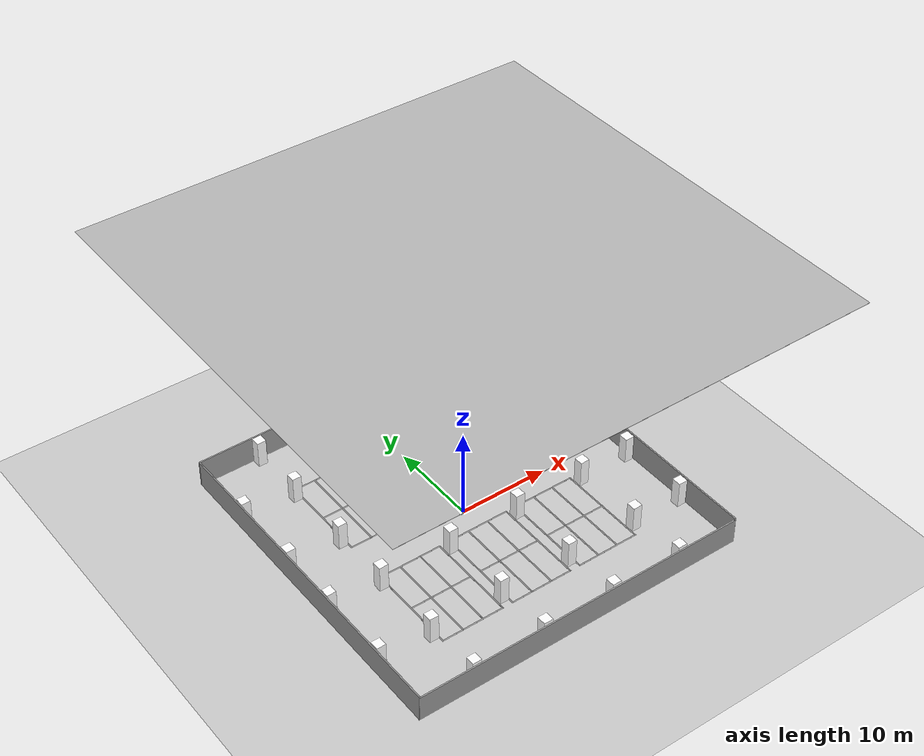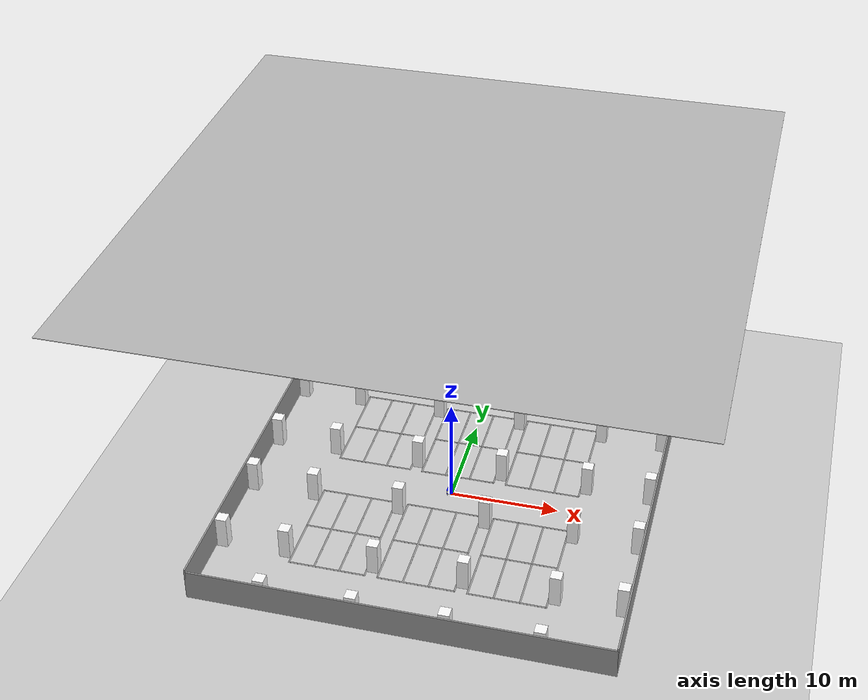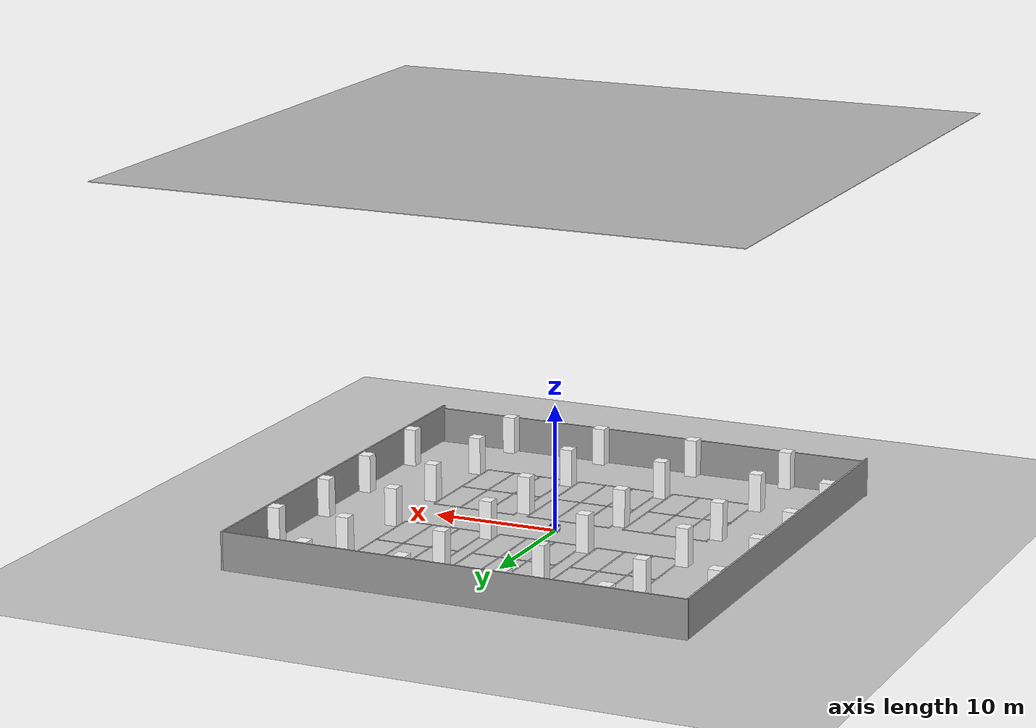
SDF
<?xml version="1.0" ?>
<sdf version="1.5">
  <world name="default">
    <light name='overhead' type='directional'>
      <cast_shadows>0</cast_shadows>
      <pose frame=''>-5 -5 3 0 -0 0</pose>
      <diffuse>0.8 0.8 0.7 1</diffuse>
      <specular>0.1 0.1 0.1 1</specular>
      <attenuation>
        <range>3</range>
        <constant>0</constant>
        <linear>0.9</linear>
        <quadratic>0.001</quadratic>
      </attenuation>
      <direction>0 0 -1</direction>
    </light>

    <scene><grid>false</grid></scene>

    <!-- Invisible ground plane -->
    <model name="ground_plane">
      <static>true</static>
      <link name="ground_link">
        <collision name="ground_collision">
          <geometry>
            <plane>
              <normal>0 0 1</normal>
              <size>100 100</size>
            </plane>
          </geometry>
          <surface><friction><ode><mu>100</mu><mu2>50</mu2></ode></friction></surface>
        </collision>
        <visual name="visual">
          <cast_shadows>false</cast_shadows>
          <geometry>
            <plane>
              <normal>0 0 1</normal>
              <size>100 100</size>
            </plane>
          </geometry>
          <material>
            <script>
              <uri>file://media/materials/scripts/gazebo.material</uri>
              <name>Gazebo/Grey</name>
            </script>
          </material>
        </visual>
      </link>
    </model>

    <model name="ceiling">
      <pose>0 0 30 0 0 0</pose>
      <link name="body">
        <visual name="visual">
          <geometry>
            <plane>
              <normal>0 0 1</normal>
              <size>50 50</size>
            </plane>
          </geometry>
        </visual>
      </link>
      <static>true</static>
    </model>

    <gui>
      <camera name="chase_cam">
        <track_visual>
          <name>trailer</name>
          <static>true</static>
          <use_model_frame>true</use_model_frame>
          <xyz>-1.5 0 -0.2</xyz>
        </track_visual>
      </camera>
    </gui>

    <joint name="trailer_joint" type="fixed">
      <parent>ground_link</parent>
      <child>trailer</child>
    </joint>
    <model name="trailer">
      <pose>0 0 .30 0 0 0</pose>
      <static>false</static>
      <link name="trailer">
        <inertial>
          <mass>10.0</mass>
          <inertia> <!-- inertias are tricky to compute -->
            <!-- http://gazebosim.org/tutorials?tut=inertia&cat=build_robot -->
            <ixx>0.349</ixx>       <!-- for a box: ixx = 0.083 * mass * (y*y + z*z) -->
            <ixy>0.0</ixy>         <!-- for a box: ixy = 0 -->
            <ixz>0.0</ixz>         <!-- for a box: ixz = 0 -->
            <iyy>0.600</iyy>       <!-- for a box: iyy = 0.083 * mass * (x*x + z*z) -->
            <iyz>0.0</iyz>         <!-- for a box: iyz = 0 -->
            <izz>0.683</izz>       <!-- for a box: izz = 0.083 * mass * (x*x + y*y) -->
          </inertia>
        </inertial>
        <collision name="trailer_collision">
          <geometry><box><size>0.749 0.509 0.398</size></box></geometry>
        </collision>
        <visual name="visual">
          <geometry><box><size>0.749 0.509 0.398</size></box></geometry>
          <material>
            <ambient>.1 0.1 1 1</ambient>
            <diffuse>.1 0.1 1 1</diffuse>
            <specular>0 0 0 1</specular>
            <emissive>0 0 0 0</emissive>
          </material>
        </visual>
      </link>

      <joint name="kingpin_joint" type="fixed">
        <parent>trailer</parent>
        <child>kingpin</child>
      </joint>
      <link name='kingpin'>
        <pose>0.30 0 -.215  0 0 0</pose>
        <inertial>
          <mass>0.005</mass>
          <inertia>
            <ixx>0.001</ixx><ixy>0.0</ixy><ixz>0.0</ixz>
              <iyy>0.001</iyy><iyz>0.0</iyz>
                <izz>0.0001</izz>
          </inertia>
        </inertial>
        <collision name="kingpin_collision">
          <geometry>
            <cylinder><radius>0.005</radius><length>0.03</length></cylinder>
          </geometry>
        </collision>
        <visual name="visual">
          <geometry>
            <cylinder><radius>0.005</radius><length>0.03</length></cylinder>
          </geometry>
          <material> <!-- red -->
            <ambient>1 0 0 1</ambient>
            <diffuse>1 0 0 1</diffuse>
            <specular>0 0 0 1</specular>
            <emissive>0 0 0 0</emissive>
          </material>
        </visual>
      </link>

      <joint name="kingpin2_joint" type="fixed">
        <parent>trailer</parent>
        <child>kingpin2</child>
      </joint>
      <link name='kingpin2'>
        <pose>-0.30 0 -.215  0 0 0</pose>
        <inertial>
          <mass>0.005</mass>
          <inertia>
            <ixx>0.001</ixx><ixy>0.0</ixy><ixz>0.0</ixz>
              <iyy>0.001</iyy><iyz>0.0</iyz>
                <izz>0.0001</izz>
          </inertia>
        </inertial>
        <collision name="kingpin2_collision">
          <geometry>
            <cylinder><radius>0.005</radius><length>0.03</length></cylinder>
          </geometry>
        </collision>
        <visual name="visual">
          <geometry>
            <cylinder><radius>0.005</radius><length>0.03</length></cylinder>
          </geometry>
          <material> <!-- red -->
            <ambient>1 0 0 1</ambient>
            <diffuse>1 0 0 1</diffuse>
            <specular>0 0 0 1</specular>
            <emissive>0 0 0 0</emissive>
          </material>
        </visual>
      </link>

      <joint name="Lhitch_joint" type="fixed">
        <parent>kingpin2</parent>
        <child>Lhitch</child>
      </joint>
      <link name='Lhitch'>
        <pose relative_to="kingpin2">0 -.15 0  1.57079 0 0</pose>
        <inertial>
          <mass>0.005</mass>
          <inertia>
            <ixx>0.001</ixx><ixy>0.0</ixy><ixz>0.0</ixz>
              <iyy>0.001</iyy><iyz>0.0</iyz>
                <izz>0.0001</izz>
          </inertia>
        </inertial>
        <collision name="Lhitch_collision">
          <geometry>
            <cylinder><radius>0.005</radius><length>0.02</length></cylinder>
          </geometry>
        </collision>
        <visual name="visual">
          <geometry>
            <cylinder><radius>0.005</radius><length>0.02</length></cylinder>
          </geometry>
          <material> <!-- red -->
            <ambient>1 0 0 1</ambient>
            <diffuse>1 0 0 1</diffuse>
            <specular>0 0 0 1</specular>
            <emissive>0 0 0 0</emissive>
          </material>
        </visual>
      </link>

      <joint name="Rhitch_joint" type="fixed">
        <parent>kingpin2</parent>
        <child>Rhitch</child>
      </joint>
      <link name='Rhitch'>
        <pose relative_to="kingpin2">0 .15 0  1.57079 0 0</pose>
        <inertial>
          <mass>0.005</mass>
          <inertia>
            <ixx>0.001</ixx><ixy>0.0</ixy><ixz>0.0</ixz>
              <iyy>0.001</iyy><iyz>0.0</iyz>
                <izz>0.0001</izz>
          </inertia>
        </inertial>
        <collision name="Rhitch_collision">
          <geometry>
            <cylinder><radius>0.005</radius><length>0.02</length></cylinder>
          </geometry>
        </collision>
        <visual name="visual">
          <geometry>
            <cylinder><radius>0.005</radius><length>0.02</length></cylinder>
          </geometry>
          <material> <!-- red -->
            <ambient>1 0 0 1</ambient>
            <diffuse>1 0 0 1</diffuse>
            <specular>0 0 0 1</specular>
            <emissive>0 0 0 0</emissive>
          </material>
        </visual>
      </link>

      <joint name="aruco_front_joint" type="fixed">
        <child>aruco_front</child>
        <parent>trailer</parent>
      </joint>
      <link name='aruco_front'>
        <pose>0.375 0 0  0 -1.57079 3.14159</pose>
        <visual name='visual'>
          <geometry><box><size>0.3 0.51 1e-6</size></box></geometry>
          <material>
            <script>
              <uri>model://materials/scripts</uri>
              <uri>model://materials/textures</uri>
              <name>aruco_front_marker</name>
            </script>
            <ambient>1 1 1 1</ambient>
            <diffuse>1 1 1 1</diffuse>
            <specular>.7 .7 .7 1</specular>
            <shader type='vertex'><normal_map>__default__</normal_map></shader>
          </material>
          <cast_shadows>0</cast_shadows>
          <transparency>0</transparency>
        </visual>
      </link>

      <joint name='aruco_right_joint' type='fixed'>
        <child>aruco_right</child>
        <parent>trailer</parent>
      </joint>
      <link name='aruco_right'>
        <pose>0 -0.255 0 0 -1.57079 1.57079</pose>
        <visual name='visual'>
          <geometry><box><size>0.3 0.75 1e-6</size></box></geometry>
          <material>
            <script>
              <uri>model://materials/scripts</uri>
              <uri>model://materials/textures</uri>
              <name>aruco_right_marker</name>
            </script>
            <ambient>1 1 1 1</ambient>
            <diffuse>1 1 1 1</diffuse>
            <specular>.7 .7 .7 1</specular>
            <shader type='vertex'><normal_map>__default__</normal_map></shader>
          </material>
          <cast_shadows>0</cast_shadows>
          <transparency>0</transparency>
        </visual>
      </link>

      <joint name="aruco_rear_joint" type="fixed">
        <child>aruco_rear</child>
        <parent>trailer</parent>
      </joint>
      <link name='aruco_rear'>
        <pose>-0.375 0 0  0 -1.57079 0</pose>
        <visual name='visual'>
          <geometry><box><size>0.3 0.51 1e-6</size></box></geometry>
          <material>
            <script>
              <uri>model://materials/scripts</uri>
              <uri>model://materials/textures</uri>
              <name>aruco_rear_marker</name>
            </script>
            <ambient>1 1 1 1</ambient>
            <diffuse>1 1 1 1</diffuse>
            <specular>.7 .7 .7 1</specular>
            <shader type='vertex'><normal_map>__default__</normal_map></shader>
          </material>
          <cast_shadows>0</cast_shadows>
          <transparency>0</transparency>
        </visual>
      </link>

      <joint name='aruco_left_joint' type='fixed'>
        <child>aruco_left</child>
        <parent>trailer</parent>
      </joint>
      <link name='aruco_left'>
        <pose>0 0.255 0 0 1.57079 -1.57079</pose>
        <visual name='visual'>
          <geometry><box><size>0.3 0.75 1e-6</size></box></geometry>
          <material>
            <script>
              <uri>model://materials/scripts</uri>
              <uri>model://materials/textures</uri>
              <name>aruco_left_marker</name>
            </script>
            <ambient>1 1 1 1</ambient>
            <diffuse>1 1 1 1</diffuse>
            <specular>.7 .7 .7 1</specular>
            <shader type='vertex'><normal_map>__default__</normal_map></shader>
          </material>
          <cast_shadows>0</cast_shadows>
          <transparency>0</transparency>
        </visual>
      </link>

      <joint name='aruco_bottom_joint' type='fixed'>
        <child>aruco_bottom</child>
        <parent>trailer</parent>
      </joint>
      <link name='aruco_bottom'>
        <pose>0 0 -0.2  0 0 -1.57079</pose>
        <visual name='visual'>
          <geometry><box><size>0.51 0.75 1e-6</size></box></geometry>
          <material>
            <script>
              <uri>model://materials/scripts</uri>
              <uri>model://materials/textures</uri>
              <name>aruco_bottom_marker</name>
            </script>
            <ambient>1 1 1 1</ambient>
            <diffuse>1 1 1 1</diffuse>
            <specular>.7 .7 .7 1</specular>
            <shader type='vertex'><normal_map>__default__</normal_map></shader>
          </material>
          <cast_shadows>0</cast_shadows>
          <transparency>0</transparency>
        </visual>
      </link>

      <link name="leg1">
        <pose>0.30 0.23 -0.25 0 0 0</pose>
        <inertial>
          <mass>0.25</mass>
          <inertia>
            <ixx>0.083</ixx><ixy>0.0</ixy><ixz>0.0</ixz>
            <iyy>0.083</iyy><iyz>0.0</iyz>
            <izz>0.083</izz>
          </inertia>
        </inertial>
        <collision name="leg1_collision">
          <geometry>
            <cylinder><radius>0.02</radius><length>0.25</length></cylinder>
          </geometry>
        </collision>
        <visual name="visual">
          <geometry>
            <cylinder><radius>0.02</radius><length>0.25</length></cylinder>
          </geometry>
          <material>
            <ambient>0.7 0.7 0.7 1</ambient>
            <diffuse>0.7 0.7 0.7 1</diffuse>
          </material>
        </visual>
      </link>
      <joint type="fixed" name="leg1_joint">
        <child>leg1</child>
        <parent>trailer</parent>
      </joint>

      <link name="leg2">
        <static>false</static>
        <pose>0.30 -0.23 -0.25 0 0 0</pose>
        <inertial>
          <inertia>
            <ixx>0.083</ixx><ixy>0.0</ixy><ixz>0.0</ixz>
            <iyy>0.083</iyy><iyz>0.0</iyz>
            <izz>0.083</izz>
          </inertia>
          <mass>0.25</mass>
        </inertial>
        <collision name="leg2_collision">
          <geometry>
            <cylinder><radius>0.02</radius><length>0.25</length></cylinder>
          </geometry>
        </collision>
        <visual name="visual">
          <geometry>
            <cylinder><radius>0.02</radius><length>0.25</length></cylinder>
          </geometry>
          <material>
            <ambient>0.7 0.7 0.7 1</ambient>
            <diffuse>0.7 0.7 0.7 1</diffuse>
          </material>
        </visual>
      </link>
      <joint type="fixed" name="leg2_joint">
        <child>leg2</child>
        <parent>trailer</parent>
      </joint>

      <link name="leg3">
        <static>false</static>
        <pose>-0.30 0.23 -0.25 0 0 0</pose>
        <inertial>
          <mass>0.25</mass>
          <inertia>
            <ixx>0.083</ixx><ixy>0.0</ixy><ixz>0.0</ixz>
            <iyy>0.083</iyy><iyz>0.0</iyz>
            <izz>0.083</izz>
          </inertia>
        </inertial>
        <collision name="leg3_collision">
          <geometry>
            <cylinder><radius>0.02</radius><length>0.25</length></cylinder>
          </geometry>
        </collision>
        <visual name="visual">
          <geometry>
            <cylinder><radius>0.02</radius><length>0.25</length></cylinder>
          </geometry>
          <material>
            <ambient>0.7 0.7 0.7 1</ambient>
            <diffuse>0.7 0.7 0.7 1</diffuse>
          </material>
        </visual>
      </link>
      <joint type="fixed" name="leg3_joint">
        <child>leg3</child>
        <parent>trailer</parent>
      </joint>

      <link name="leg4">
        <pose>-0.30 -0.23 -0.25 0 0 0</pose>
        <inertial>
          <mass>0.25</mass>
          <inertia>
            <ixx>0.083</ixx><ixy>0.0</ixy><ixz>0.0</ixz>
            <iyy>0.083</iyy><iyz>0.0</iyz>
            <izz>0.083</izz>
          </inertia>
        </inertial>
        <collision name="leg4_collision">
          <geometry>
            <cylinder><radius>0.02</radius><length>0.25</length></cylinder>
          </geometry>
        </collision>
        <visual name="visual">
          <geometry>
            <cylinder><radius>0.02</radius><length>0.25</length></cylinder>
          </geometry>
          <material>
            <ambient>0.7 0.7 0.7 1</ambient>
            <diffuse>0.7 0.7 0.7 1</diffuse>
          </material>
        </visual>
      </link>
      <joint type="fixed" name="leg4_joint">
        <child>leg4</child>
        <parent>trailer</parent>
      </joint>
    </model>

    <model name='column1'>
      <pose>12.075 11.45 1.5 0 -0 0</pose>
      <link name='link'>
        <collision name='collision'>
          <geometry>
            <box>
              <size>1 1 3</size>
            </box>
          </geometry>
          <max_contacts>10</max_contacts>
          <surface>
            <contact>
              <ode/>
            </contact>
            <bounce/>
            <friction>
              <torsional>
                <ode/>
              </torsional>
              <ode/>
            </friction>
          </surface>
        </collision>
        <visual name='visual'>
          <geometry>
            <box>
              <size>1 1 3</size>
            </box>
          </geometry>
          <material>
            <script>
              <uri>model://materials/scripts</uri>
              <uri>model://materials/textures</uri>
              <name>column/parking</name>
            </script>
            <ambient>1 1 1 1</ambient>
            <diffuse>1 1 1 1</diffuse>
            <specular>0 0 0 1</specular>
            <emissive>1 1 1 0</emissive>
            <shader type='vertex'>
              <normal_map>__default__</normal_map>
            </shader>
          </material>
        </visual>
        <self_collide>0</self_collide>
        <enable_wind>0</enable_wind>
        <kinematic>0</kinematic>
      </link>
      <static>1</static>
    </model>

    <model name='column2'>
      <pose>4.025 11.45 1.5 0 -0 0</pose>
      <link name='link'>
        <collision name='collision'>
          <geometry>
            <box>
              <size>1 1 3</size>
            </box>
          </geometry>
          <max_contacts>10</max_contacts>
          <surface>
            <contact>
              <ode/>
            </contact>
            <bounce/>
            <friction>
              <torsional>
                <ode/>
              </torsional>
              <ode/>
            </friction>
          </surface>
        </collision>
        <visual name='visual'>
          <geometry>
            <box>
              <size>1 1 3</size>
            </box>
          </geometry>
          <material>
            <script>
              <uri>model://materials/scripts</uri>
              <uri>model://materials/textures</uri>
              <name>column/parking</name>
            </script>
            <ambient>1 1 1 1</ambient>
            <diffuse>1 1 1 1</diffuse>
            <specular>0 0 0 1</specular>
            <emissive>1 1 1 0</emissive>
            <shader type='vertex'>
              <normal_map>__default__</normal_map>
            </shader>
          </material>
        </visual>
        <self_collide>0</self_collide>
        <enable_wind>0</enable_wind>
        <kinematic>0</kinematic>
      </link>
      <static>1</static>
    </model>

    <model name='column3'>
      <pose>-4.025 11.45 1.5 0 -0 0</pose>
      <link name='link'>
        <collision name='collision'>
          <geometry>
            <box>
              <size>1 1 3</size>
            </box>
          </geometry>
          <max_contacts>10</max_contacts>
          <surface>
            <contact>
              <ode/>
            </contact>
            <bounce/>
            <friction>
              <torsional>
                <ode/>
              </torsional>
              <ode/>
            </friction>
          </surface>
        </collision>
        <visual name='visual'>
          <geometry>
            <box>
              <size>1 1 3</size>
            </box>
          </geometry>
          <material>
            <script>
              <uri>model://materials/scripts</uri>
              <uri>model://materials/textures</uri>
              <name>column/parking</name>
            </script>
            <ambient>1 1 1 1</ambient>
            <diffuse>1 1 1 1</diffuse>
            <specular>0 0 0 1</specular>
            <emissive>1 1 1 0</emissive>
            <shader type='vertex'>
              <normal_map>__default__</normal_map>
            </shader>
          </material>
        </visual>
        <self_collide>0</self_collide>
        <enable_wind>0</enable_wind>
        <kinematic>0</kinematic>
      </link>
      <static>1</static>
    </model>

    <model name='column4'>
      <pose>-12.075 11.45 1.5 0 -0 0</pose>
      <link name='link'>
        <collision name='collision'>
          <geometry>
            <box>
              <size>1 1 3</size>
            </box>
          </geometry>
          <max_contacts>10</max_contacts>
          <surface>
            <contact>
              <ode/>
            </contact>
            <bounce/>
            <friction>
              <torsional>
                <ode/>
              </torsional>
              <ode/>
            </friction>
          </surface>
        </collision>
        <visual name='visual'>
          <geometry>
            <box>
              <size>1 1 3</size>
            </box>
          </geometry>
          <material>
            <script>
              <uri>model://materials/scripts</uri>
              <uri>model://materials/textures</uri>
              <name>column/parking</name>
            </script>
            <ambient>1 1 1 1</ambient>
            <diffuse>1 1 1 1</diffuse>
            <specular>0 0 0 1</specular>
            <emissive>1 1 1 0</emissive>
            <shader type='vertex'>
              <normal_map>__default__</normal_map>
            </shader>
          </material>
        </visual>
        <self_collide>0</self_collide>
        <enable_wind>0</enable_wind>
        <kinematic>0</kinematic>
      </link>
      <static>1</static>
    </model>

    <model name='column5'>
      <pose>12.075 3.45 1.5 0 -0 0</pose>
      <link name='link'>
        <collision name='collision'>
          <geometry>
            <box>
              <size>1 1 3</size>
            </box>
          </geometry>
          <max_contacts>10</max_contacts>
          <surface>
            <contact>
              <ode/>
            </contact>
            <bounce/>
            <friction>
              <torsional>
                <ode/>
              </torsional>
              <ode/>
            </friction>
          </surface>
        </collision>
        <visual name='visual'>
          <geometry>
            <box>
              <size>1 1 3</size>
            </box>
          </geometry>
          <material>
            <script>
              <uri>model://materials/scripts</uri>
              <uri>model://materials/textures</uri>
              <name>column/parking</name>
            </script>
            <ambient>1 1 1 1</ambient>
            <diffuse>1 1 1 1</diffuse>
            <specular>0 0 0 1</specular>
            <emissive>1 1 1 0</emissive>
            <shader type='vertex'>
              <normal_map>__default__</normal_map>
            </shader>
          </material>
        </visual>
        <self_collide>0</self_collide>
        <enable_wind>0</enable_wind>
        <kinematic>0</kinematic>
      </link>
      <static>1</static>
    </model>

    <model name='column6'>
      <pose>4.025 3.45 1.5 0 -0 0</pose>
      <link name='link'>
        <collision name='collision'>
          <geometry>
            <box>
              <size>1 1 3</size>
            </box>
          </geometry>
          <max_contacts>10</max_contacts>
          <surface>
            <contact>
              <ode/>
            </contact>
            <bounce/>
            <friction>
              <torsional>
                <ode/>
              </torsional>
              <ode/>
            </friction>
          </surface>
        </collision>
        <visual name='visual'>
          <geometry>
            <box>
              <size>1 1 3</size>
            </box>
          </geometry>
          <material>
            <script>
              <uri>model://materials/scripts</uri>
              <uri>model://materials/textures</uri>
              <name>column/parking</name>
            </script>
            <ambient>1 1 1 1</ambient>
            <diffuse>1 1 1 1</diffuse>
            <specular>0 0 0 1</specular>
            <emissive>1 1 1 0</emissive>
            <shader type='vertex'>
              <normal_map>__default__</normal_map>
            </shader>
          </material>
        </visual>
        <self_collide>0</self_collide>
        <enable_wind>0</enable_wind>
        <kinematic>0</kinematic>
      </link>
      <static>1</static>
    </model>

    <model name='column7'>
      <pose>-4.025 3.45 1.5 0 -0 0</pose>
      <link name='link'>
        <collision name='collision'>
          <geometry>
            <box>
              <size>1 1 3</size>
            </box>
          </geometry>
          <max_contacts>10</max_contacts>
          <surface>
            <contact>
              <ode/>
            </contact>
            <bounce/>
            <friction>
              <torsional>
                <ode/>
              </torsional>
              <ode/>
            </friction>
          </surface>
        </collision>
        <visual name='visual'>
          <geometry>
            <box>
              <size>1 1 3</size>
            </box>
          </geometry>
          <material>
            <script>
              <uri>model://materials/scripts</uri>
              <uri>model://materials/textures</uri>
              <name>column/parking</name>
            </script>
            <ambient>1 1 1 1</ambient>
            <diffuse>1 1 1 1</diffuse>
            <specular>0 0 0 1</specular>
            <emissive>1 1 1 0</emissive>
            <shader type='vertex'>
              <normal_map>__default__</normal_map>
            </shader>
          </material>
        </visual>
        <self_collide>0</self_collide>
        <enable_wind>0</enable_wind>
        <kinematic>0</kinematic>
      </link>
      <static>1</static>
    </model>

    <model name='column8'>
      <pose>-12.075 3.45 1.5 0 -0 0</pose>
      <link name='link'>
        <collision name='collision'>
          <geometry>
            <box>
              <size>1 1 3</size>
            </box>
          </geometry>
          <max_contacts>10</max_contacts>
          <surface>
            <contact>
              <ode/>
            </contact>
            <bounce/>
            <friction>
              <torsional>
                <ode/>
              </torsional>
              <ode/>
            </friction>
          </surface>
        </collision>
        <visual name='visual'>
          <geometry>
            <box>
              <size>1 1 3</size>
            </box>
          </geometry>
          <material>
            <script>
              <uri>model://materials/scripts</uri>
              <uri>model://materials/textures</uri>
              <name>column/parking</name>
            </script>
            <ambient>1 1 1 1</ambient>
            <diffuse>1 1 1 1</diffuse>
            <specular>0 0 0 1</specular>
            <emissive>1 1 1 0</emissive>
            <shader type='vertex'>
              <normal_map>__default__</normal_map>
            </shader>
          </material>
        </visual>
        <self_collide>0</self_collide>
        <enable_wind>0</enable_wind>
        <kinematic>0</kinematic>
      </link>
      <static>1</static>
    </model>

    <model name='column9'>
      <pose>12.075 -11.45 1.5 0 -0 0</pose>
      <link name='link'>
        <collision name='collision'>
          <geometry>
            <box>
              <size>1 1 3</size>
            </box>
          </geometry>
          <max_contacts>10</max_contacts>
          <surface>
            <contact>
              <ode/>
            </contact>
            <bounce/>
            <friction>
              <torsional>
                <ode/>
              </torsional>
              <ode/>
            </friction>
          </surface>
        </collision>
        <visual name='visual'>
          <geometry>
            <box>
              <size>1 1 3</size>
            </box>
          </geometry>
          <material>
            <script>
              <uri>model://materials/scripts</uri>
              <uri>model://materials/textures</uri>
              <name>column/parking</name>
            </script>
            <ambient>1 1 1 1</ambient>
            <diffuse>1 1 1 1</diffuse>
            <specular>0 0 0 1</specular>
            <emissive>1 1 1 0</emissive>
            <shader type='vertex'>
              <normal_map>__default__</normal_map>
            </shader>
          </material>
        </visual>
        <self_collide>0</self_collide>
        <enable_wind>0</enable_wind>
        <kinematic>0</kinematic>
      </link>
      <static>1</static>
    </model>
    <model name='column10'>
      <pose>4.025 -11.45 1.5 0 -0 0</pose>
      <link name='link'>
        <collision name='collision'>
          <geometry>
            <box>
              <size>1 1 3</size>
            </box>
          </geometry>
          <max_contacts>10</max_contacts>
          <surface>
            <contact>
              <ode/>
            </contact>
            <bounce/>
            <friction>
              <torsional>
                <ode/>
              </torsional>
              <ode/>
            </friction>
          </surface>
        </collision>
        <visual name='visual'>
          <geometry>
            <box>
              <size>1 1 3</size>
            </box>
          </geometry>
          <material>
            <script>
              <uri>model://materials/scripts</uri>
              <uri>model://materials/textures</uri>
              <name>column/parking</name>
            </script>
            <ambient>1 1 1 1</ambient>
            <diffuse>1 1 1 1</diffuse>
            <specular>0 0 0 1</specular>
            <emissive>1 1 1 0</emissive>
            <shader type='vertex'>
              <normal_map>__default__</normal_map>
            </shader>
          </material>
        </visual>
        <self_collide>0</self_collide>
        <enable_wind>0</enable_wind>
        <kinematic>0</kinematic>
      </link>
      <static>1</static>
    </model>
  <model name='column11'>
      <pose>-4.025 -11.45 1.5 0 -0 0</pose>
      <link name='link'>
        <collision name='collision'>
          <geometry>
            <box>
              <size>1 1 3</size>
            </box>
          </geometry>
          <max_contacts>10</max_contacts>
          <surface>
            <contact>
              <ode/>
            </contact>
            <bounce/>
            <friction>
              <torsional>
                <ode/>
              </torsional>
              <ode/>
            </friction>
          </surface>
        </collision>
        <visual name='visual'>
          <geometry>
            <box>
              <size>1 1 3</size>
            </box>
          </geometry>
          <material>
            <script>
              <uri>model://materials/scripts</uri>
              <uri>model://materials/textures</uri>
              <name>column/parking</name>
            </script>
            <ambient>1 1 1 1</ambient>
            <diffuse>1 1 1 1</diffuse>
            <specular>0 0 0 1</specular>
            <emissive>1 1 1 0</emissive>
            <shader type='vertex'>
              <normal_map>__default__</normal_map>
            </shader>
          </material>
        </visual>
        <self_collide>0</self_collide>
        <enable_wind>0</enable_wind>
        <kinematic>0</kinematic>
      </link>
      <static>1</static>
    </model>
    <model name='column12'>
      <pose>-12.075 -11.45 1.5 0 -0 0</pose>
      <link name='link'>
        <collision name='collision'>
          <geometry>
            <box>
              <size>1 1 3</size>
            </box>
          </geometry>
          <max_contacts>10</max_contacts>
          <surface>
            <contact>
              <ode/>
            </contact>
            <bounce/>
            <friction>
              <torsional>
                <ode/>
              </torsional>
              <ode/>
            </friction>
          </surface>
        </collision>
        <visual name='visual'>
          <geometry>
            <box>
              <size>1 1 3</size>
            </box>
          </geometry>
          <material>
            <script>
              <uri>model://materials/scripts</uri>
              <uri>model://materials/textures</uri>
              <name>column/parking</name>
            </script>
            <ambient>1 1 1 1</ambient>
            <diffuse>1 1 1 1</diffuse>
            <specular>0 0 0 1</specular>
            <emissive>1 1 1 0</emissive>
            <shader type='vertex'>
              <normal_map>__default__</normal_map>
            </shader>
          </material>
        </visual>
        <self_collide>0</self_collide>
        <enable_wind>0</enable_wind>
        <kinematic>0</kinematic>
      </link>
      <static>1</static>
    </model>

    <model name='column13'>
      <pose>12.075 -3.45 1.5 0 -0 0</pose>
      <link name='link'>
        <collision name='collision'>
          <geometry>
            <box>
              <size>1 1 3</size>
            </box>
          </geometry>
          <max_contacts>10</max_contacts>
          <surface>
            <contact>
              <ode/>
            </contact>
            <bounce/>
            <friction>
              <torsional>
                <ode/>
              </torsional>
              <ode/>
            </friction>
          </surface>
        </collision>
        <visual name='visual'>
          <geometry>
            <box>
              <size>1 1 3</size>
            </box>
          </geometry>
          <material>
            <script>
              <uri>model://materials/scripts</uri>
              <uri>model://materials/textures</uri>
              <name>column/parking</name>
            </script>
            <ambient>1 1 1 1</ambient>
            <diffuse>1 1 1 1</diffuse>
            <specular>0 0 0 1</specular>
            <emissive>1 1 1 0</emissive>
            <shader type='vertex'>
              <normal_map>__default__</normal_map>
            </shader>
          </material>
        </visual>
        <self_collide>0</self_collide>
        <enable_wind>0</enable_wind>
        <kinematic>0</kinematic>
      </link>
      <static>1</static>
    </model>

    <model name='column14'>
      <pose>4.025 -3.45 1.5 0 -0 0</pose>
      <link name='link'>
        <collision name='collision'>
          <geometry>
            <box>
              <size>1 1 3</size>
            </box>
          </geometry>
          <max_contacts>10</max_contacts>
          <surface>
            <contact>
              <ode/>
            </contact>
            <bounce/>
            <friction>
              <torsional>
                <ode/>
              </torsional>
              <ode/>
            </friction>
          </surface>
        </collision>
        <visual name='visual'>
          <geometry>
            <box>
              <size>1 1 3</size>
            </box>
          </geometry>
          <material>
            <script>
              <uri>model://materials/scripts</uri>
              <uri>model://materials/textures</uri>
              <name>column/parking</name>
            </script>
            <ambient>1 1 1 1</ambient>
            <diffuse>1 1 1 1</diffuse>
            <specular>0 0 0 1</specular>
            <emissive>1 1 1 0</emissive>
            <shader type='vertex'>
              <normal_map>__default__</normal_map>
            </shader>
          </material>
        </visual>
        <self_collide>0</self_collide>
        <enable_wind>0</enable_wind>
        <kinematic>0</kinematic>
      </link>
      <static>1</static>
    </model>

    <model name='column15'>
      <pose>-4.025 -3.45 1.5 0 -0 0</pose>
      <link name='link'>
        <collision name='collision'>
          <geometry>
            <box>
              <size>1 1 3</size>
            </box>
          </geometry>
          <max_contacts>10</max_contacts>
          <surface>
            <contact>
              <ode/>
            </contact>
            <bounce/>
            <friction>
              <torsional>
                <ode/>
              </torsional>
              <ode/>
            </friction>
          </surface>
        </collision>
        <visual name='visual'>
          <geometry>
            <box>
              <size>1 1 3</size>
            </box>
          </geometry>
          <material>
            <script>
              <uri>model://materials/scripts</uri>
              <uri>model://materials/textures</uri>
              <name>column/parking</name>
            </script>
            <ambient>1 1 1 1</ambient>
            <diffuse>1 1 1 1</diffuse>
            <specular>0 0 0 1</specular>
            <emissive>1 1 1 0</emissive>
            <shader type='vertex'>
              <normal_map>__default__</normal_map>
            </shader>
          </material>
        </visual>
        <self_collide>0</self_collide>
        <enable_wind>0</enable_wind>
        <kinematic>0</kinematic>
      </link>
      <static>1</static>
    </model>

    <model name='column16'>
      <pose>-12.075 -3.45 1.5 0 -0 0</pose>
      <link name='link'>
        <collision name='collision'>
          <geometry>
            <box>
              <size>1 1 3</size>
            </box>
          </geometry>
          <max_contacts>10</max_contacts>
          <surface>
            <contact>
              <ode/>
            </contact>
            <bounce/>
            <friction>
              <torsional>
                <ode/>
              </torsional>
              <ode/>
            </friction>
          </surface>
        </collision>
        <visual name='visual'>
          <geometry>
            <box>
              <size>1 1 3</size>
            </box>
          </geometry>
          <material>
            <script>
              <uri>model://materials/scripts</uri>
              <uri>model://materials/textures</uri>
              <name>column/parking</name>
            </script>
            <ambient>1 1 1 1</ambient>
            <diffuse>1 1 1 1</diffuse>
            <specular>0 0 0 1</specular>
            <emissive>1 1 1 0</emissive>
            <shader type='vertex'>
              <normal_map>__default__</normal_map>
            </shader>
          </material>
        </visual>
        <self_collide>0</self_collide>
        <enable_wind>0</enable_wind>
        <kinematic>0</kinematic>
      </link>
      <static>1</static>
    </model>

    <model name='column_s1'>
      <pose>17.875 3.45 1.5 0 -0 0</pose>
      <link name='link'>
        <collision name='collision'>
          <geometry>
            <box>
              <size>1 1 3</size>
            </box>
          </geometry>
          <max_contacts>10</max_contacts>
          <surface>
            <contact>
              <ode/>
            </contact>
            <bounce/>
            <friction>
              <torsional>
                <ode/>
              </torsional>
              <ode/>
            </friction>
          </surface>
        </collision>
        <visual name='visual'>
          <geometry>
            <box>
              <size>1 1 3</size>
            </box>
          </geometry>
          <material>
            <script>
              <uri>model://materials/scripts</uri>
              <uri>model://materials/textures</uri>
              <name>column/parking</name>
            </script>
            <ambient>1 1 1 1</ambient>
            <diffuse>1 1 1 1</diffuse>
            <specular>0 0 0 1</specular>
            <emissive>1 1 1 0</emissive>
            <shader type='vertex'>
              <normal_map>__default__</normal_map>
            </shader>
          </material>
        </visual>
        <self_collide>0</self_collide>
        <enable_wind>0</enable_wind>
        <kinematic>0</kinematic>
      </link>
      <static>1</static>
    </model>
    <model name='column_s2'>
      <pose>17.875 11.45 1.5 0 -0 0</pose>
      <link name='link'>
        <collision name='collision'>
          <geometry>
            <box>
              <size>1 1 3</size>
            </box>
          </geometry>
          <max_contacts>10</max_contacts>
          <surface>
            <contact>
              <ode/>
            </contact>
            <bounce/>
            <friction>
              <torsional>
                <ode/>
              </torsional>
              <ode/>
            </friction>
          </surface>
        </collision>
        <visual name='visual'>
          <geometry>
            <box>
              <size>1 1 3</size>
            </box>
          </geometry>
          <material>
            <script>
              <uri>model://materials/scripts</uri>
              <uri>model://materials/textures</uri>
              <name>column/parking</name>
            </script>
            <ambient>1 1 1 1</ambient>
            <diffuse>1 1 1 1</diffuse>
            <specular>0 0 0 1</specular>
            <emissive>1 1 1 0</emissive>
            <shader type='vertex'>
              <normal_map>__default__</normal_map>
            </shader>
          </material>
        </visual>
        <self_collide>0</self_collide>
        <enable_wind>0</enable_wind>
        <kinematic>0</kinematic>
      </link>
      <static>1</static>
    </model>

    <model name='column_s3'>
      <pose>12.075 17.95 1.5 0 -0 0</pose>
      <link name='link'>
        <collision name='collision'>
          <geometry>
            <box>
              <size>1 1 3</size>
            </box>
          </geometry>
          <max_contacts>10</max_contacts>
          <surface>
            <contact>
              <ode/>
            </contact>
            <bounce/>
            <friction>
              <torsional>
                <ode/>
              </torsional>
              <ode/>
            </friction>
          </surface>
        </collision>
        <visual name='visual'>
          <geometry>
            <box>
              <size>1 1 3</size>
            </box>
          </geometry>
          <material>
            <script>
              <uri>model://materials/scripts</uri>
              <uri>model://materials/textures</uri>
              <name>column/parking</name>
            </script>
            <ambient>1 1 1 1</ambient>
            <diffuse>1 1 1 1</diffuse>
            <specular>0 0 0 1</specular>
            <emissive>1 1 1 0</emissive>
            <shader type='vertex'>
              <normal_map>__default__</normal_map>
            </shader>
          </material>
        </visual>
        <self_collide>0</self_collide>
        <enable_wind>0</enable_wind>
        <kinematic>0</kinematic>
      </link>
      <static>1</static>
    </model>

    <model name='column_s4'>
      <pose>4.025 17.95 1.5 0 -0 0</pose>
      <link name='link'>
        <collision name='collision'>
          <geometry>
            <box>
              <size>1 1 3</size>
            </box>
          </geometry>
          <max_contacts>10</max_contacts>
          <surface>
            <contact>
              <ode/>
            </contact>
            <bounce/>
            <friction>
              <torsional>
                <ode/>
              </torsional>
              <ode/>
            </friction>
          </surface>
        </collision>
        <visual name='visual'>
          <geometry>
            <box>
              <size>1 1 3</size>
            </box>
          </geometry>
          <material>
            <script>
              <uri>model://materials/scripts</uri>
              <uri>model://materials/textures</uri>
              <name>column/parking</name>
            </script>
            <ambient>1 1 1 1</ambient>
            <diffuse>1 1 1 1</diffuse>
            <specular>0 0 0 1</specular>
            <emissive>1 1 1 0</emissive>
            <shader type='vertex'>
              <normal_map>__default__</normal_map>
            </shader>
          </material>
        </visual>
        <self_collide>0</self_collide>
        <enable_wind>0</enable_wind>
        <kinematic>0</kinematic>
      </link>
      <static>1</static>
    </model>
    <model name='column_s5'>
      <pose>-4.025 17.95 1.5 0 -0 0</pose>
      <link name='link'>
        <collision name='collision'>
          <geometry>
            <box>
              <size>1 1 3</size>
            </box>
          </geometry>
          <max_contacts>10</max_contacts>
          <surface>
            <contact>
              <ode/>
            </contact>
            <bounce/>
            <friction>
              <torsional>
                <ode/>
              </torsional>
              <ode/>
            </friction>
          </surface>
        </collision>
        <visual name='visual'>
          <geometry>
            <box>
              <size>1 1 3</size>
            </box>
          </geometry>
          <material>
            <script>
              <uri>model://materials/scripts</uri>
              <uri>model://materials/textures</uri>
              <name>column/parking</name>
            </script>
            <ambient>1 1 1 1</ambient>
            <diffuse>1 1 1 1</diffuse>
            <specular>0 0 0 1</specular>
            <emissive>1 1 1 0</emissive>
            <shader type='vertex'>
              <normal_map>__default__</normal_map>
            </shader>
          </material>
        </visual>
        <self_collide>0</self_collide>
        <enable_wind>0</enable_wind>
        <kinematic>0</kinematic>
      </link>
      <static>1</static>
    </model>
    <model name='column_s6'>
      <pose>-12.075 17.95 1.5 0 -0 0</pose>
      <link name='link'>
        <collision name='collision'>
          <geometry>
            <box>
              <size>1 1 3</size>
            </box>
          </geometry>
          <max_contacts>10</max_contacts>
          <surface>
            <contact>
              <ode/>
            </contact>
            <bounce/>
            <friction>
              <torsional>
                <ode/>
              </torsional>
              <ode/>
            </friction>
          </surface>
        </collision>
        <visual name='visual'>
          <geometry>
            <box>
              <size>1 1 3</size>
            </box>
          </geometry>
          <material>
            <script>
              <uri>model://materials/scripts</uri>
              <uri>model://materials/textures</uri>
              <name>column/parking</name>
            </script>
            <ambient>1 1 1 1</ambient>
            <diffuse>1 1 1 1</diffuse>
            <specular>0 0 0 1</specular>
            <emissive>1 1 1 0</emissive>
            <shader type='vertex'>
              <normal_map>__default__</normal_map>
            </shader>
          </material>
        </visual>
        <self_collide>0</self_collide>
        <enable_wind>0</enable_wind>
        <kinematic>0</kinematic>
      </link>
      <static>1</static>
    </model>

    <model name='column_s7'>
      <pose>-17.875 11.45 1.5 0 -0 0</pose>
      <link name='link'>
        <collision name='collision'>
          <geometry>
            <box>
              <size>1 1 3</size>
            </box>
          </geometry>
          <max_contacts>10</max_contacts>
          <surface>
            <contact>
              <ode/>
            </contact>
            <bounce/>
            <friction>
              <torsional>
                <ode/>
              </torsional>
              <ode/>
            </friction>
          </surface>
        </collision>
        <visual name='visual'>
          <geometry>
            <box>
              <size>1 1 3</size>
            </box>
          </geometry>
          <material>
            <script>
              <uri>model://materials/scripts</uri>
              <uri>model://materials/textures</uri>
              <name>column/parking</name>
            </script>
            <ambient>1 1 1 1</ambient>
            <diffuse>1 1 1 1</diffuse>
            <specular>0 0 0 1</specular>
            <emissive>1 1 1 0</emissive>
            <shader type='vertex'>
              <normal_map>__default__</normal_map>
            </shader>
          </material>
        </visual>
        <self_collide>0</self_collide>
        <enable_wind>0</enable_wind>
        <kinematic>0</kinematic>
      </link>
      <static>1</static>
    </model>

    <model name='column_s8'>
      <pose>-17.875 3.45 1.5 0 -0 0</pose>
      <link name='link'>
        <collision name='collision'>
          <geometry>
            <box>
              <size>1 1 3</size>
            </box>
          </geometry>
          <max_contacts>10</max_contacts>
          <surface>
            <contact>
              <ode/>
            </contact>
            <bounce/>
            <friction>
              <torsional>
                <ode/>
              </torsional>
              <ode/>
            </friction>
          </surface>
        </collision>
        <visual name='visual'>
          <geometry>
            <box>
              <size>1 1 3</size>
            </box>
          </geometry>
          <material>
            <script>
              <uri>model://materials/scripts</uri>
              <uri>model://materials/textures</uri>
              <name>column/parking</name>
            </script>
            <ambient>1 1 1 1</ambient>
            <diffuse>1 1 1 1</diffuse>
            <specular>0 0 0 1</specular>
            <emissive>1 1 1 0</emissive>
            <shader type='vertex'>
              <normal_map>__default__</normal_map>
            </shader>
          </material>
        </visual>
        <self_collide>0</self_collide>
        <enable_wind>0</enable_wind>
        <kinematic>0</kinematic>
      </link>
      <static>1</static>
    </model>

    <model name='column_s9'>
      <pose>-17.875 -3.45 1.5 0 -0 0</pose>
      <link name='link'>
        <collision name='collision'>
          <geometry>
            <box>
              <size>1 1 3</size>
            </box>
          </geometry>
          <max_contacts>10</max_contacts>
          <surface>
            <contact>
              <ode/>
            </contact>
            <bounce/>
            <friction>
              <torsional>
                <ode/>
              </torsional>
              <ode/>
            </friction>
          </surface>
        </collision>
        <visual name='visual'>
          <geometry>
            <box>
              <size>1 1 3</size>
            </box>
          </geometry>
          <material>
            <script>
              <uri>model://materials/scripts</uri>
              <uri>model://materials/textures</uri>
              <name>column/parking</name>
            </script>
            <ambient>1 1 1 1</ambient>
            <diffuse>1 1 1 1</diffuse>
            <specular>0 0 0 1</specular>
            <emissive>1 1 1 0</emissive>
            <shader type='vertex'>
              <normal_map>__default__</normal_map>
            </shader>
          </material>
        </visual>
        <self_collide>0</self_collide>
        <enable_wind>0</enable_wind>
        <kinematic>0</kinematic>
      </link>
      <static>1</static>
    </model>

    <model name='column_s10'>
      <pose>-17.875 -11.45 1.5 0 -0 0</pose>
      <link name='link'>
        <collision name='collision'>
          <geometry>
            <box>
              <size>1 1 3</size>
            </box>
          </geometry>
          <max_contacts>10</max_contacts>
          <surface>
            <contact>
              <ode/>
            </contact>
            <bounce/>
            <friction>
              <torsional>
                <ode/>
              </torsional>
              <ode/>
            </friction>
          </surface>
        </collision>
        <visual name='visual'>
          <geometry>
            <box>
              <size>1 1 3</size>
            </box>
          </geometry>
          <material>
            <script>
              <uri>model://materials/scripts</uri>
              <uri>model://materials/textures</uri>
              <name>column/parking</name>
            </script>
            <ambient>1 1 1 1</ambient>
            <diffuse>1 1 1 1</diffuse>
            <specular>0 0 0 1</specular>
            <emissive>1 1 1 0</emissive>
            <shader type='vertex'>
              <normal_map>__default__</normal_map>
            </shader>
          </material>
        </visual>
        <self_collide>0</self_collide>
        <enable_wind>0</enable_wind>
        <kinematic>0</kinematic>
      </link>
      <static>1</static>
    </model>

    <model name='column_s11'>
      <pose>-12.075 -17.95 1.5 0 -0 0</pose>
      <link name='link'>
        <collision name='collision'>
          <geometry>
            <box>
              <size>1 1 3</size>
            </box>
          </geometry>
          <max_contacts>10</max_contacts>
          <surface>
            <contact>
              <ode/>
            </contact>
            <bounce/>
            <friction>
              <torsional>
                <ode/>
              </torsional>
              <ode/>
            </friction>
          </surface>
        </collision>
        <visual name='visual'>
          <geometry>
            <box>
              <size>1 1 3</size>
            </box>
          </geometry>
          <material>
            <script>
              <uri>model://materials/scripts</uri>
              <uri>model://materials/textures</uri>
              <name>column/parking</name>
            </script>
            <ambient>1 1 1 1</ambient>
            <diffuse>1 1 1 1</diffuse>
            <specular>0 0 0 1</specular>
            <emissive>1 1 1 0</emissive>
            <shader type='vertex'>
              <normal_map>__default__</normal_map>
            </shader>
          </material>
        </visual>
        <self_collide>0</self_collide>
        <enable_wind>0</enable_wind>
        <kinematic>0</kinematic>
      </link>
      <static>1</static>
    </model>

    <model name='column_s12'>
      <pose>-4.025 -17.95 1.5 0 -0 0</pose>
      <link name='link'>
        <collision name='collision'>
          <geometry>
            <box>
              <size>1 1 3</size>
            </box>
          </geometry>
          <max_contacts>10</max_contacts>
          <surface>
            <contact>
              <ode/>
            </contact>
            <bounce/>
            <friction>
              <torsional>
                <ode/>
              </torsional>
              <ode/>
            </friction>
          </surface>
        </collision>
        <visual name='visual'>
          <geometry>
            <box>
              <size>1 1 3</size>
            </box>
          </geometry>
          <material>
            <script>
              <uri>model://materials/scripts</uri>
              <uri>model://materials/textures</uri>
              <name>column/parking</name>
            </script>
            <ambient>1 1 1 1</ambient>
            <diffuse>1 1 1 1</diffuse>
            <specular>0 0 0 1</specular>
            <emissive>1 1 1 0</emissive>
            <shader type='vertex'>
              <normal_map>__default__</normal_map>
            </shader>
          </material>
        </visual>
        <self_collide>0</self_collide>
        <enable_wind>0</enable_wind>
        <kinematic>0</kinematic>
      </link>
      <static>1</static>
    </model>

    <model name='column_s13'>
      <pose>4.025 -17.95 1.5 0 -0 0</pose>
      <link name='link'>
        <collision name='collision'>
          <geometry>
            <box>
              <size>1 1 3</size>
            </box>
          </geometry>
          <max_contacts>10</max_contacts>
          <surface>
            <contact>
              <ode/>
            </contact>
            <bounce/>
            <friction>
              <torsional>
                <ode/>
              </torsional>
              <ode/>
            </friction>
          </surface>
        </collision>
        <visual name='visual'>
          <geometry>
            <box>
              <size>1 1 3</size>
            </box>
          </geometry>
          <material>
            <script>
              <uri>model://materials/scripts</uri>
              <uri>model://materials/textures</uri>
              <name>column/parking</name>
            </script>
            <ambient>1 1 1 1</ambient>
            <diffuse>1 1 1 1</diffuse>
            <specular>0 0 0 1</specular>
            <emissive>1 1 1 0</emissive>
            <shader type='vertex'>
              <normal_map>__default__</normal_map>
            </shader>
          </material>
        </visual>
        <self_collide>0</self_collide>
        <enable_wind>0</enable_wind>
        <kinematic>0</kinematic>
      </link>
      <static>1</static>
    </model>

    <model name='column_s14'>
      <pose>12.075 -17.95 1.5 0 -0 0</pose>
      <link name='link'>
        <collision name='collision'>
          <geometry>
            <box>
              <size>1 1 3</size>
            </box>
          </geometry>
          <max_contacts>10</max_contacts>
          <surface>
            <contact>
              <ode/>
            </contact>
            <bounce/>
            <friction>
              <torsional>
                <ode/>
              </torsional>
              <ode/>
            </friction>
          </surface>
        </collision>
        <visual name='visual'>
          <geometry>
            <box>
              <size>1 1 3</size>
            </box>
          </geometry>
          <material>
            <script>
              <uri>model://materials/scripts</uri>
              <uri>model://materials/textures</uri>
              <name>column/parking</name>
            </script>
            <ambient>1 1 1 1</ambient>
            <diffuse>1 1 1 1</diffuse>
            <specular>0 0 0 1</specular>
            <emissive>1 1 1 0</emissive>
            <shader type='vertex'>
              <normal_map>__default__</normal_map>
            </shader>
          </material>
        </visual>
        <self_collide>0</self_collide>
        <enable_wind>0</enable_wind>
        <kinematic>0</kinematic>
      </link>
      <static>1</static>
    </model>
    <model name='column_s15'>
      <pose>17.875 -11.45 1.5 0 -0 0</pose>
      <link name='link'>
        <collision name='collision'>
          <geometry>
            <box>
              <size>1 1 3</size>
            </box>
          </geometry>
          <max_contacts>10</max_contacts>
          <surface>
            <contact>
              <ode/>
            </contact>
            <bounce/>
            <friction>
              <torsional>
                <ode/>
              </torsional>
              <ode/>
            </friction>
          </surface>
        </collision>
        <visual name='visual'>
          <geometry>
            <box>
              <size>1 1 3</size>
            </box>
          </geometry>
          <material>
            <script>
              <uri>model://materials/scripts</uri>
              <uri>model://materials/textures</uri>
              <name>column/parking</name>
            </script>
            <ambient>1 1 1 1</ambient>
            <diffuse>1 1 1 1</diffuse>
            <specular>0 0 0 1</specular>
            <emissive>1 1 1 0</emissive>
            <shader type='vertex'>
              <normal_map>__default__</normal_map>
            </shader>
          </material>
        </visual>
        <self_collide>0</self_collide>
        <enable_wind>0</enable_wind>
        <kinematic>0</kinematic>
      </link>
      <static>1</static>
    </model>

    <model name='column_s16'>
      <pose>17.875 -3.45 1.5 0 -0 0</pose>
      <link name='link'>
        <collision name='collision'>
          <geometry>
            <box>
              <size>1 1 3</size>
            </box>
          </geometry>
          <max_contacts>10</max_contacts>
          <surface>
            <contact>
              <ode/>
            </contact>
            <bounce/>
            <friction>
              <torsional>
                <ode/>
              </torsional>
              <ode/>
            </friction>
          </surface>
        </collision>
        <visual name='visual'>
          <geometry>
            <box>
              <size>1 1 3</size>
            </box>
          </geometry>
          <material>
            <script>
              <uri>model://materials/scripts</uri>
              <uri>model://materials/textures</uri>
              <name>column/parking</name>
            </script>
            <ambient>1 1 1 1</ambient>
            <diffuse>1 1 1 1</diffuse>
            <specular>0 0 0 1</specular>
            <emissive>1 1 1 0</emissive>
            <shader type='vertex'>
              <normal_map>__default__</normal_map>
            </shader>
          </material>
        </visual>
        <self_collide>0</self_collide>
        <enable_wind>0</enable_wind>
        <kinematic>0</kinematic>
      </link>
      <static>1</static>
    </model>

<model name='wall_outer'>
    <pose>0 0 0 0 -0 0</pose>
    <link name='Wall_0'>
      <collision name='Wall_0_Collision'>
        <geometry>
          <box>
            <size>37.35 0.15 3</size>
          </box>
        </geometry>
        <pose>0 0 1.5 0 -0 0</pose>
      </collision>
      <visual name='Wall_0_Visual'>
        <pose>0 0 1.5 0 -0 0</pose>
        <geometry>
          <box>
            <size>37.35 0.15 3</size>
          </box>
        </geometry>
        <material>
          <script>
            <uri>file://media/materials/scripts/gazebo.material</uri>
            <name>Gazebo/Grey</name>
          </script>
          <ambient>1 1 1 1</ambient>
        </material>
        <meta>
          <layer>0</layer>
        </meta>
      </visual>
      <pose>18.525 0 0 0 -0 1.5708</pose>
    </link>
    <link name='Wall_1'>
      <collision name='Wall_1_Collision'>
        <geometry>
          <box>
            <size>37.2 0.15 3</size>
          </box>
        </geometry>
        <pose>0 0 1.5 0 -0 0</pose>
      </collision>
      <visual name='Wall_1_Visual'>
        <pose>0 0 1.5 0 -0 0</pose>
        <geometry>
          <box>
            <size>37.2 0.15 3</size>
          </box>
        </geometry>
        <material>
          <script>
            <uri>file://media/materials/scripts/gazebo.material</uri>
            <name>Gazebo/Grey</name>
          </script>
          <ambient>1 1 1 1</ambient>
        </material>
        <meta>
          <layer>0</layer>
        </meta>
      </visual>
      <pose>0 18.6 0 0 -0 3.14159</pose>
    </link>
    <link name='Wall_2'>
      <collision name='Wall_2_Collision'>
        <geometry>
          <box>
            <size>37.35 0.15 3</size>
          </box>
        </geometry>
        <pose>0 0 1.5 0 -0 0</pose>
      </collision>
      <visual name='Wall_2_Visual'>
        <pose>0 0 1.5 0 -0 0</pose>
        <geometry>
          <box>
            <size>37.35 0.15 3</size>
          </box>
        </geometry>
        <material>
          <script>
            <uri>file://media/materials/scripts/gazebo.material</uri>
            <name>Gazebo/Grey</name>
          </script>
          <ambient>1 1 1 1</ambient>
        </material>
        <meta>
          <layer>0</layer>
        </meta>
      </visual>
      <pose>-18.525 0 0 0 -0 -1.5708</pose>
    </link>
    <link name='Wall_3'>
      <collision name='Wall_3_Collision'>
        <geometry>
          <box>
            <size>37.2 0.15 3</size>
          </box>
        </geometry>
        <pose>0 0 1.25 0 -0 0</pose>
      </collision>
      <visual name='Wall_3_Visual'>
        <pose>0 0 1.25 0 -0 0</pose>
        <geometry>
          <box>
            <size>37.2 0.15 3</size>
          </box>
        </geometry>
        <material>
          <script>
            <uri>file://media/materials/scripts/gazebo.material</uri>
            <name>Gazebo/Grey</name>
          </script>
          <ambient>1 1 1 1</ambient>
        </material>
        <meta>
          <layer>0</layer>
        </meta>
      </visual>
      <pose>0 -18.6 0 0 -0 0</pose>
    </link>
    <static>1</static>
  </model>
<model name='parking_line1'>
      <pose>5.7875 6.2625 0 0 -0 0</pose>
      <link name='Wall_27'>
        <collision name='Wall_27_Collision'>
          <geometry>
            <box>
              <size>7.05 0.15 0.005</size>
            </box>
          </geometry>
          <pose>0 0 0.0025 0 -0 0</pose>
          <max_contacts>10</max_contacts>
          <surface>
            <contact>
              <ode/>
            </contact>
            <bounce/>
            <friction>
              <torsional>
                <ode/>
              </torsional>
              <ode/>
            </friction>
          </surface>
        </collision>
        <visual name='Wall_27_Visual'>
          <pose>0 0 0.0025 0 -0 0</pose>
          <geometry>
            <box>
              <size>7.05 0.15 0.005</size>
            </box>
          </geometry>
          <material>
            <script>
              <uri>file://media/materials/scripts/gazebo.material</uri>
              <name>Gazebo/Grey</name>
            </script>
            <ambient>1 1 1 1</ambient>
          </material>
          <meta>
            <layer>0</layer>
          </meta>
        </visual>
        <pose>2.2625 -3.8125 0 0 -0 0</pose>
        <self_collide>0</self_collide>
        <enable_wind>0</enable_wind>
        <kinematic>0</kinematic>
      </link>
      <link name='Wall_28'>
        <collision name='Wall_28_Collision'>
          <geometry>
            <box>
              <size>10.15 0.15 0.005</size>
            </box>
          </geometry>
          <pose>0 0 0.0025 0 -0 0</pose>
          <max_contacts>10</max_contacts>
          <surface>
            <contact>
              <ode/>
            </contact>
            <bounce/>
            <friction>
              <torsional>
                <ode/>
              </torsional>
              <ode/>
            </friction>
          </surface>
        </collision>
        <visual name='Wall_28_Visual'>
          <pose>0 0 0.0025 0 -0 0</pose>
          <geometry>
            <box>
              <size>10.15 0.15 0.005</size>
            </box>
          </geometry>
          <material>
            <script>
              <uri>file://media/materials/scripts/gazebo.material</uri>
              <name>Gazebo/Grey</name>
            </script>
            <ambient>1 1 1 1</ambient>
          </material>
          <meta>
            <layer>0</layer>
          </meta>
        </visual>
        <pose>5.7125 1.1875 0 0 -0 1.5708</pose>
        <self_collide>0</self_collide>
        <enable_wind>0</enable_wind>
        <kinematic>0</kinematic>
      </link>
      <link name='Wall_29'>
        <collision name='Wall_29_Collision'>
          <geometry>
            <box>
              <size>7.05 0.15 0.005</size>
            </box>
          </geometry>
          <pose>0 0 0.0025 0 -0 0</pose>
          <max_contacts>10</max_contacts>
          <surface>
            <contact>
              <ode/>
            </contact>
            <bounce/>
            <friction>
              <torsional>
                <ode/>
              </torsional>
              <ode/>
            </friction>
          </surface>
        </collision>
        <visual name='Wall_29_Visual'>
          <pose>0 0 0.0025 0 -0 0</pose>
          <geometry>
            <box>
              <size>7.05 0.15 0.005</size>
            </box>
          </geometry>
          <material>
            <script>
              <uri>file://media/materials/scripts/gazebo.material</uri>
              <name>Gazebo/Grey</name>
            </script>
            <ambient>1 1 1 1</ambient>
          </material>
          <meta>
            <layer>0</layer>
          </meta>
        </visual>
        <pose>2.2625 6.1875 0 0 -0 3.14159</pose>
        <self_collide>0</self_collide>
        <enable_wind>0</enable_wind>
        <kinematic>0</kinematic>
      </link>
      <link name='Wall_30'>
        <collision name='Wall_30_Collision'>
          <geometry>
            <box>
              <size>10.15 0.15 0.005</size>
            </box>
          </geometry>
          <pose>0 0 0.0025 0 -0 0</pose>
          <max_contacts>10</max_contacts>
          <surface>
            <contact>
              <ode/>
            </contact>
            <bounce/>
            <friction>
              <torsional>
                <ode/>
              </torsional>
              <ode/>
            </friction>
          </surface>
        </collision>
        <visual name='Wall_30_Visual'>
          <pose>0 0 0.0025 0 -0 0</pose>
          <geometry>
            <box>
              <size>10.15 0.15 0.005</size>
            </box>
          </geometry>
          <material>
            <script>
              <uri>file://media/materials/scripts/gazebo.material</uri>
              <name>Gazebo/Grey</name>
            </script>
            <ambient>1 1 1 1</ambient>
          </material>
          <meta>
            <layer>0</layer>
          </meta>
        </visual>
        <pose>-1.1875 1.1875 0 0 -0 -1.5708</pose>
        <self_collide>0</self_collide>
        <enable_wind>0</enable_wind>
        <kinematic>0</kinematic>
      </link>
      <link name='Wall_32'>
        <collision name='Wall_32_Collision'>
          <geometry>
            <box>
              <size>7.05 0.15 0.005</size>
            </box>
          </geometry>
          <pose>0 0 0.0025 0 -0 0</pose>
          <max_contacts>10</max_contacts>
          <surface>
            <contact>
              <ode/>
            </contact>
            <bounce/>
            <friction>
              <torsional>
                <ode/>
              </torsional>
              <ode/>
            </friction>
          </surface>
        </collision>
        <visual name='Wall_32_Visual'>
          <pose>0 0 0.0025 0 -0 0</pose>
          <geometry>
            <box>
              <size>7.05 0.15 0.005</size>
            </box>
          </geometry>
          <material>
            <script>
              <uri>file://media/materials/scripts/gazebo.material</uri>
              <name>Gazebo/Grey</name>
            </script>
            <ambient>1 1 1 1</ambient>
          </material>
          <meta>
            <layer>0</layer>
          </meta>
        </visual>
        <pose>2.2625 1.1875 0 0 -0 0</pose>
        <self_collide>0</self_collide>
        <enable_wind>0</enable_wind>
        <kinematic>0</kinematic>
      </link>
      <link name='Wall_34'>
        <collision name='Wall_34_Collision'>
          <geometry>
            <box>
              <size>10.15 0.15 0.005</size>
            </box>
          </geometry>
          <pose>0 0 0.0025 0 -0 0</pose>
          <max_contacts>10</max_contacts>
          <surface>
            <contact>
              <ode/>
            </contact>
            <bounce/>
            <friction>
              <torsional>
                <ode/>
              </torsional>
              <ode/>
            </friction>
          </surface>
        </collision>
        <visual name='Wall_34_Visual'>
          <pose>0 0 0.0025 0 -0 0</pose>
          <geometry>
            <box>
              <size>10.15 0.15 0.005</size>
            </box>
          </geometry>
          <material>
            <script>
              <uri>file://media/materials/scripts/gazebo.material</uri>
              <name>Gazebo/Grey</name>
            </script>
            <ambient>1 1 1 1</ambient>
          </material>
          <meta>
            <layer>0</layer>
          </meta>
        </visual>
        <pose>3.4125 1.1875 0 0 -0 1.5708</pose>
        <self_collide>0</self_collide>
        <enable_wind>0</enable_wind>
        <kinematic>0</kinematic>
      </link>
      <link name='Wall_36'>
        <collision name='Wall_36_Collision'>
          <geometry>
            <box>
              <size>10.15 0.15 0.005</size>
            </box>
          </geometry>
          <pose>0 0 0.0025 0 -0 0</pose>
          <max_contacts>10</max_contacts>
          <surface>
            <contact>
              <ode/>
            </contact>
            <bounce/>
            <friction>
              <torsional>
                <ode/>
              </torsional>
              <ode/>
            </friction>
          </surface>
        </collision>
        <visual name='Wall_36_Visual'>
          <pose>0 0 0.0025 0 -0 0</pose>
          <geometry>
            <box>
              <size>10.15 0.15 0.005</size>
            </box>
          </geometry>
          <material>
            <script>
              <uri>file://media/materials/scripts/gazebo.material</uri>
              <name>Gazebo/Grey</name>
            </script>
            <ambient>1 1 1 1</ambient>
          </material>
          <meta>
            <layer>0</layer>
          </meta>
        </visual>
        <pose>1.1125 1.1875 0 0 -0 1.5708</pose>
        <self_collide>0</self_collide>
        <enable_wind>0</enable_wind>
        <kinematic>0</kinematic>
      </link>
      <static>1</static>
    </model>
    <model name='parking_line2'>
      <pose>-7.5e-05 6.26258 0 0 -0 0</pose>
      <link name='Wall_11'>
        <collision name='Wall_11_Collision'>
          <geometry>
            <box>
              <size>10.15 0.15 0.005</size>
            </box>
          </geometry>
          <pose>0 0 0.0025 0 -0 0</pose>
          <max_contacts>10</max_contacts>
          <surface>
            <contact>
              <ode/>
            </contact>
            <bounce/>
            <friction>
              <torsional>
                <ode/>
              </torsional>
              <ode/>
            </friction>
          </surface>
        </collision>
        <visual name='Wall_11_Visual'>
          <pose>0 0 0.0025 0 -0 0</pose>
          <geometry>
            <box>
              <size>10.15 0.15 0.005</size>
            </box>
          </geometry>
          <material>
            <script>
              <uri>file://media/materials/scripts/gazebo.material</uri>
              <name>Gazebo/Grey</name>
            </script>
            <ambient>1 1 1 1</ambient>
          </material>
          <meta>
            <layer>0</layer>
          </meta>
        </visual>
        <pose>1.15007 1.18742 0 0 -0 1.5708</pose>
        <self_collide>0</self_collide>
        <enable_wind>0</enable_wind>
        <kinematic>0</kinematic>
      </link>
      <link name='Wall_2'>
        <collision name='Wall_2_Collision'>
          <geometry>
            <box>
              <size>7.05 0.15 0.005</size>
            </box>
          </geometry>
          <pose>0 0 0.0025 0 -0 0</pose>
          <max_contacts>10</max_contacts>
          <surface>
            <contact>
              <ode/>
            </contact>
            <bounce/>
            <friction>
              <torsional>
                <ode/>
              </torsional>
              <ode/>
            </friction>
          </surface>
        </collision>
        <visual name='Wall_2_Visual'>
          <pose>0 0 0.0025 0 -0 0</pose>
          <geometry>
            <box>
              <size>7.05 0.15 0.005</size>
            </box>
          </geometry>
          <material>
            <script>
              <uri>file://media/materials/scripts/gazebo.material</uri>
              <name>Gazebo/Grey</name>
            </script>
            <ambient>1 1 1 1</ambient>
          </material>
          <meta>
            <layer>0</layer>
          </meta>
        </visual>
        <pose>7.5e-05 -3.81257 0 0 -0 0</pose>
        <self_collide>0</self_collide>
        <enable_wind>0</enable_wind>
        <kinematic>0</kinematic>
      </link>
      <link name='Wall_3'>
        <collision name='Wall_3_Collision'>
          <geometry>
            <box>
              <size>10.15 0.15 0.005</size>
            </box>
          </geometry>
          <pose>0 0 0.0025 0 -0 0</pose>
          <max_contacts>10</max_contacts>
          <surface>
            <contact>
              <ode/>
            </contact>
            <bounce/>
            <friction>
              <torsional>
                <ode/>
              </torsional>
              <ode/>
            </friction>
          </surface>
        </collision>
        <visual name='Wall_3_Visual'>
          <pose>0 0 0.0025 0 -0 0</pose>
          <geometry>
            <box>
              <size>10.15 0.15 0.005</size>
            </box>
          </geometry>
          <material>
            <script>
              <uri>file://media/materials/scripts/gazebo.material</uri>
              <name>Gazebo/Grey</name>
            </script>
            <ambient>1 1 1 1</ambient>
          </material>
          <meta>
            <layer>0</layer>
          </meta>
        </visual>
        <pose>3.45008 1.18742 0 0 -0 1.5708</pose>
        <self_collide>0</self_collide>
        <enable_wind>0</enable_wind>
        <kinematic>0</kinematic>
      </link>
      <link name='Wall_4'>
        <collision name='Wall_4_Collision'>
          <geometry>
            <box>
              <size>7.03 0.15 0.005</size>
            </box>
          </geometry>
          <pose>0 0 0.0025 0 -0 0</pose>
          <max_contacts>10</max_contacts>
          <surface>
            <contact>
              <ode/>
            </contact>
            <bounce/>
            <friction>
              <torsional>
                <ode/>
              </torsional>
              <ode/>
            </friction>
          </surface>
        </collision>
        <visual name='Wall_4_Visual'>
          <pose>0 0 0.0025 0 -0 0</pose>
          <geometry>
            <box>
              <size>7.03 0.15 0.005</size>
            </box>
          </geometry>
          <material>
            <script>
              <uri>file://media/materials/scripts/gazebo.material</uri>
              <name>Gazebo/Grey</name>
            </script>
            <ambient>1 1 1 1</ambient>
          </material>
          <meta>
            <layer>0</layer>
          </meta>
        </visual>
        <pose>0.010075 6.18743 0 0 -0 3.14159</pose>
        <self_collide>0</self_collide>
        <enable_wind>0</enable_wind>
        <kinematic>0</kinematic>
      </link>
      <link name='Wall_5'>
        <collision name='Wall_5_Collision'>
          <geometry>
            <box>
              <size>10.15 0.15 0.005</size>
            </box>
          </geometry>
          <pose>0 0 0.0025 0 -0 0</pose>
          <max_contacts>10</max_contacts>
          <surface>
            <contact>
              <ode/>
            </contact>
            <bounce/>
            <friction>
              <torsional>
                <ode/>
              </torsional>
              <ode/>
            </friction>
          </surface>
        </collision>
        <visual name='Wall_5_Visual'>
          <pose>0 0 0.0025 0 -0 0</pose>
          <geometry>
            <box>
              <size>10.15 0.15 0.005</size>
            </box>
          </geometry>
          <material>
            <script>
              <uri>file://media/materials/scripts/gazebo.material</uri>
              <name>Gazebo/Grey</name>
            </script>
            <ambient>1 1 1 1</ambient>
          </material>
          <meta>
            <layer>0</layer>
          </meta>
        </visual>
        <pose>-3.45 1.18742 0 0 -0 -1.5708</pose>
        <self_collide>0</self_collide>
        <enable_wind>0</enable_wind>
        <kinematic>0</kinematic>
      </link>
      <link name='Wall_7'>
        <collision name='Wall_7_Collision'>
          <geometry>
            <box>
              <size>7.05 0.15 0.005</size>
            </box>
          </geometry>
          <pose>0 0 0.0025 0 -0 0</pose>
          <max_contacts>10</max_contacts>
          <surface>
            <contact>
              <ode/>
            </contact>
            <bounce/>
            <friction>
              <torsional>
                <ode/>
              </torsional>
              <ode/>
            </friction>
          </surface>
        </collision>
        <visual name='Wall_7_Visual'>
          <pose>0 0 0.0025 0 -0 0</pose>
          <geometry>
            <box>
              <size>7.05 0.15 0.005</size>
            </box>
          </geometry>
          <material>
            <script>
              <uri>file://media/materials/scripts/gazebo.material</uri>
              <name>Gazebo/Grey</name>
            </script>
            <ambient>1 1 1 1</ambient>
          </material>
          <meta>
            <layer>0</layer>
          </meta>
        </visual>
        <pose>7.5e-05 1.18742 0 0 -0 0</pose>
        <self_collide>0</self_collide>
        <enable_wind>0</enable_wind>
        <kinematic>0</kinematic>
      </link>
      <link name='Wall_9'>
        <collision name='Wall_9_Collision'>
          <geometry>
            <box>
              <size>10.15 0.15 0.005</size>
            </box>
          </geometry>
          <pose>0 0 0.0025 0 -0 0</pose>
          <max_contacts>10</max_contacts>
          <surface>
            <contact>
              <ode/>
            </contact>
            <bounce/>
            <friction>
              <torsional>
                <ode/>
              </torsional>
              <ode/>
            </friction>
          </surface>
        </collision>
        <visual name='Wall_9_Visual'>
          <pose>0 0 0.0025 0 -0 0</pose>
          <geometry>
            <box>
              <size>10.15 0.15 0.005</size>
            </box>
          </geometry>
          <material>
            <script>
              <uri>file://media/materials/scripts/gazebo.material</uri>
              <name>Gazebo/Grey</name>
            </script>
            <ambient>1 1 1 1</ambient>
          </material>
          <meta>
            <layer>0</layer>
          </meta>
        </visual>
        <pose>-1.14993 1.18742 0 0 -0 1.5708</pose>
        <self_collide>0</self_collide>
        <enable_wind>0</enable_wind>
        <kinematic>0</kinematic>
      </link>
      <static>1</static>
    </model>
    <model name='parking_line3'>
      <pose>-5.7875 6.2625 0 0 -0 0</pose>
      <link name='Wall_76'>
        <collision name='Wall_76_Collision'>
          <geometry>
            <box>
              <size>7.05 0.15 0.005</size>
            </box>
          </geometry>
          <pose>0 0 0.0025 0 -0 0</pose>
          <max_contacts>10</max_contacts>
          <surface>
            <contact>
              <ode/>
            </contact>
            <bounce/>
            <friction>
              <torsional>
                <ode/>
              </torsional>
              <ode/>
            </friction>
          </surface>
        </collision>
        <visual name='Wall_76_Visual'>
          <pose>0 0 0.0025 0 -0 0</pose>
          <geometry>
            <box>
              <size>7.05 0.15 0.005</size>
            </box>
          </geometry>
          <material>
            <script>
              <uri>file://media/materials/scripts/gazebo.material</uri>
              <name>Gazebo/Grey</name>
            </script>
            <ambient>1 1 1 1</ambient>
          </material>
          <meta>
            <layer>0</layer>
          </meta>
        </visual>
        <pose>-2.2625 -3.8125 0 0 -0 0</pose>
        <self_collide>0</self_collide>
        <enable_wind>0</enable_wind>
        <kinematic>0</kinematic>
      </link>
      <link name='Wall_77'>
        <collision name='Wall_77_Collision'>
          <geometry>
            <box>
              <size>10.15 0.15 0.005</size>
            </box>
          </geometry>
          <pose>0 0 0.0025 0 -0 0</pose>
          <max_contacts>10</max_contacts>
          <surface>
            <contact>
              <ode/>
            </contact>
            <bounce/>
            <friction>
              <torsional>
                <ode/>
              </torsional>
              <ode/>
            </friction>
          </surface>
        </collision>
        <visual name='Wall_77_Visual'>
          <pose>0 0 0.0025 0 -0 0</pose>
          <geometry>
            <box>
              <size>10.15 0.15 0.005</size>
            </box>
          </geometry>
          <material>
            <script>
              <uri>file://media/materials/scripts/gazebo.material</uri>
              <name>Gazebo/Grey</name>
            </script>
            <ambient>1 1 1 1</ambient>
          </material>
          <meta>
            <layer>0</layer>
          </meta>
        </visual>
        <pose>1.1875 1.1875 0 0 -0 1.5708</pose>
        <self_collide>0</self_collide>
        <enable_wind>0</enable_wind>
        <kinematic>0</kinematic>
      </link>
      <link name='Wall_78'>
        <collision name='Wall_78_Collision'>
          <geometry>
            <box>
              <size>7.05 0.15 0.005</size>
            </box>
          </geometry>
          <pose>0 0 0.0025 0 -0 0</pose>
          <max_contacts>10</max_contacts>
          <surface>
            <contact>
              <ode/>
            </contact>
            <bounce/>
            <friction>
              <torsional>
                <ode/>
              </torsional>
              <ode/>
            </friction>
          </surface>
        </collision>
        <visual name='Wall_78_Visual'>
          <pose>0 0 0.0025 0 -0 0</pose>
          <geometry>
            <box>
              <size>7.05 0.15 0.005</size>
            </box>
          </geometry>
          <material>
            <script>
              <uri>file://media/materials/scripts/gazebo.material</uri>
              <name>Gazebo/Grey</name>
            </script>
            <ambient>1 1 1 1</ambient>
          </material>
          <meta>
            <layer>0</layer>
          </meta>
        </visual>
        <pose>-2.2625 6.1875 0 0 -0 3.14159</pose>
        <self_collide>0</self_collide>
        <enable_wind>0</enable_wind>
        <kinematic>0</kinematic>
      </link>
      <link name='Wall_79'>
        <collision name='Wall_79_Collision'>
          <geometry>
            <box>
              <size>10.15 0.15 0.005</size>
            </box>
          </geometry>
          <pose>0 0 0.0025 0 -0 0</pose>
          <max_contacts>10</max_contacts>
          <surface>
            <contact>
              <ode/>
            </contact>
            <bounce/>
            <friction>
              <torsional>
                <ode/>
              </torsional>
              <ode/>
            </friction>
          </surface>
        </collision>
        <visual name='Wall_79_Visual'>
          <pose>0 0 0.0025 0 -0 0</pose>
          <geometry>
            <box>
              <size>10.15 0.15 0.005</size>
            </box>
          </geometry>
          <material>
            <script>
              <uri>file://media/materials/scripts/gazebo.material</uri>
              <name>Gazebo/Grey</name>
            </script>
            <ambient>1 1 1 1</ambient>
          </material>
          <meta>
            <layer>0</layer>
          </meta>
        </visual>
        <pose>-5.7125 1.1875 0 0 -0 -1.5708</pose>
        <self_collide>0</self_collide>
        <enable_wind>0</enable_wind>
        <kinematic>0</kinematic>
      </link>
      <link name='Wall_81'>
        <collision name='Wall_81_Collision'>
          <geometry>
            <box>
              <size>7.05 0.15 0.005</size>
            </box>
          </geometry>
          <pose>0 0 0.0025 0 -0 0</pose>
          <max_contacts>10</max_contacts>
          <surface>
            <contact>
              <ode/>
            </contact>
            <bounce/>
            <friction>
              <torsional>
                <ode/>
              </torsional>
              <ode/>
            </friction>
          </surface>
        </collision>
        <visual name='Wall_81_Visual'>
          <pose>0 0 0.0025 0 -0 0</pose>
          <geometry>
            <box>
              <size>7.05 0.15 0.005</size>
            </box>
          </geometry>
          <material>
            <script>
              <uri>file://media/materials/scripts/gazebo.material</uri>
              <name>Gazebo/Grey</name>
            </script>
            <ambient>1 1 1 1</ambient>
          </material>
          <meta>
            <layer>0</layer>
          </meta>
        </visual>
        <pose>-2.2625 1.1875 0 0 -0 3.14159</pose>
        <self_collide>0</self_collide>
        <enable_wind>0</enable_wind>
        <kinematic>0</kinematic>
      </link>
      <link name='Wall_83'>
        <collision name='Wall_83_Collision'>
          <geometry>
            <box>
              <size>10.15 0.15 0.005</size>
            </box>
          </geometry>
          <pose>0 0 0.0025 0 -0 0</pose>
          <max_contacts>10</max_contacts>
          <surface>
            <contact>
              <ode/>
            </contact>
            <bounce/>
            <friction>
              <torsional>
                <ode/>
              </torsional>
              <ode/>
            </friction>
          </surface>
        </collision>
        <visual name='Wall_83_Visual'>
          <pose>0 0 0.0025 0 -0 0</pose>
          <geometry>
            <box>
              <size>10.15 0.15 0.005</size>
            </box>
          </geometry>
          <material>
            <script>
              <uri>file://media/materials/scripts/gazebo.material</uri>
              <name>Gazebo/Grey</name>
            </script>
            <ambient>1 1 1 1</ambient>
          </material>
          <meta>
            <layer>0</layer>
          </meta>
        </visual>
        <pose>-3.4125 1.1875 0 0 -0 1.5708</pose>
        <self_collide>0</self_collide>
        <enable_wind>0</enable_wind>
        <kinematic>0</kinematic>
      </link>
      <link name='Wall_85'>
        <collision name='Wall_85_Collision'>
          <geometry>
            <box>
              <size>10.15 0.15 0.005</size>
            </box>
          </geometry>
          <pose>0 0 0.0025 0 -0 0</pose>
          <max_contacts>10</max_contacts>
          <surface>
            <contact>
              <ode/>
            </contact>
            <bounce/>
            <friction>
              <torsional>
                <ode/>
              </torsional>
              <ode/>
            </friction>
          </surface>
        </collision>
        <visual name='Wall_85_Visual'>
          <pose>0 0 0.0025 0 -0 0</pose>
          <geometry>
            <box>
              <size>10.15 0.15 0.005</size>
            </box>
          </geometry>
          <material>
            <script>
              <uri>file://media/materials/scripts/gazebo.material</uri>
              <name>Gazebo/Grey</name>
            </script>
            <ambient>1 1 1 1</ambient>
          </material>
          <meta>
            <layer>0</layer>
          </meta>
        </visual>
        <pose>-1.1125 1.1875 0 0 -0 1.5708</pose>
        <self_collide>0</self_collide>
        <enable_wind>0</enable_wind>
        <kinematic>0</kinematic>
      </link>
      <static>1</static>
    </model>

    <model name='parking_line4'>
      <pose>5.7875 -6.2625 0 0 -0 0</pose>
      <link name='Wall_41'>
        <collision name='Wall_41_Collision'>
          <geometry>
            <box>
              <size>7.05 0.15 0.005</size>
            </box>
          </geometry>
          <pose>0 0 0.0025 0 -0 0</pose>
          <max_contacts>10</max_contacts>
          <surface>
            <contact>
              <ode/>
            </contact>
            <bounce/>
            <friction>
              <torsional>
                <ode/>
              </torsional>
              <ode/>
            </friction>
          </surface>
        </collision>
        <visual name='Wall_41_Visual'>
          <pose>0 0 0.0025 0 -0 0</pose>
          <geometry>
            <box>
              <size>7.05 0.15 0.005</size>
            </box>
          </geometry>
          <material>
            <script>
              <uri>file://media/materials/scripts/gazebo.material</uri>
              <name>Gazebo/Grey</name>
            </script>
            <ambient>1 1 1 1</ambient>
          </material>
          <meta>
            <layer>0</layer>
          </meta>
        </visual>
        <pose>2.2625 3.8125 0 0 -0 0</pose>
        <self_collide>0</self_collide>
        <enable_wind>0</enable_wind>
        <kinematic>0</kinematic>
      </link>
      <link name='Wall_42'>
        <collision name='Wall_42_Collision'>
          <geometry>
            <box>
              <size>10.15 0.15 0.005</size>
            </box>
          </geometry>
          <pose>0 0 0.0025 0 -0 0</pose>
          <max_contacts>10</max_contacts>
          <surface>
            <contact>
              <ode/>
            </contact>
            <bounce/>
            <friction>
              <torsional>
                <ode/>
              </torsional>
              <ode/>
            </friction>
          </surface>
        </collision>
        <visual name='Wall_42_Visual'>
          <pose>0 0 0.0025 0 -0 0</pose>
          <geometry>
            <box>
              <size>10.15 0.15 0.005</size>
            </box>
          </geometry>
          <material>
            <script>
              <uri>file://media/materials/scripts/gazebo.material</uri>
              <name>Gazebo/Grey</name>
            </script>
            <ambient>1 1 1 1</ambient>
          </material>
          <meta>
            <layer>0</layer>
          </meta>
        </visual>
        <pose>5.7125 -1.1875 0 0 -0 1.5708</pose>
        <self_collide>0</self_collide>
        <enable_wind>0</enable_wind>
        <kinematic>0</kinematic>
      </link>
      <link name='Wall_43'>
        <collision name='Wall_43_Collision'>
          <geometry>
            <box>
              <size>7.05 0.15 0.005</size>
            </box>
          </geometry>
          <pose>0 0 0.0025 0 -0 0</pose>
          <max_contacts>10</max_contacts>
          <surface>
            <contact>
              <ode/>
            </contact>
            <bounce/>
            <friction>
              <torsional>
                <ode/>
              </torsional>
              <ode/>
            </friction>
          </surface>
        </collision>
        <visual name='Wall_43_Visual'>
          <pose>0 0 0.0025 0 -0 0</pose>
          <geometry>
            <box>
              <size>7.05 0.15 0.005</size>
            </box>
          </geometry>
          <material>
            <script>
              <uri>file://media/materials/scripts/gazebo.material</uri>
              <name>Gazebo/Grey</name>
            </script>
            <ambient>1 1 1 1</ambient>
          </material>
          <meta>
            <layer>0</layer>
          </meta>
        </visual>
        <pose>2.2625 -6.1875 0 0 -0 3.14159</pose>
        <self_collide>0</self_collide>
        <enable_wind>0</enable_wind>
        <kinematic>0</kinematic>
      </link>
      <link name='Wall_44'>
        <collision name='Wall_44_Collision'>
          <geometry>
            <box>
              <size>10.15 0.15 0.005</size>
            </box>
          </geometry>
          <pose>0 0 0.0025 0 -0 0</pose>
          <max_contacts>10</max_contacts>
          <surface>
            <contact>
              <ode/>
            </contact>
            <bounce/>
            <friction>
              <torsional>
                <ode/>
              </torsional>
              <ode/>
            </friction>
          </surface>
        </collision>
        <visual name='Wall_44_Visual'>
          <pose>0 0 0.0025 0 -0 0</pose>
          <geometry>
            <box>
              <size>10.15 0.15 0.005</size>
            </box>
          </geometry>
          <material>
            <script>
              <uri>file://media/materials/scripts/gazebo.material</uri>
              <name>Gazebo/Grey</name>
            </script>
            <ambient>1 1 1 1</ambient>
          </material>
          <meta>
            <layer>0</layer>
          </meta>
        </visual>
        <pose>-1.1875 -1.1875 0 0 -0 -1.5708</pose>
        <self_collide>0</self_collide>
        <enable_wind>0</enable_wind>
        <kinematic>0</kinematic>
      </link>
      <link name='Wall_45'>
        <collision name='Wall_45_Collision'>
          <geometry>
            <box>
              <size>7.05 0.15 0.005</size>
            </box>
          </geometry>
          <pose>0 0 0.0025 0 -0 0</pose>
          <max_contacts>10</max_contacts>
          <surface>
            <contact>
              <ode/>
            </contact>
            <bounce/>
            <friction>
              <torsional>
                <ode/>
              </torsional>
              <ode/>
            </friction>
          </surface>
        </collision>
        <visual name='Wall_45_Visual'>
          <pose>0 0 0.0025 0 -0 0</pose>
          <geometry>
            <box>
              <size>7.05 0.15 0.005</size>
            </box>
          </geometry>
          <material>
            <script>
              <uri>file://media/materials/scripts/gazebo.material</uri>
              <name>Gazebo/Grey</name>
            </script>
            <ambient>1 1 1 1</ambient>
          </material>
          <meta>
            <layer>0</layer>
          </meta>
        </visual>
        <pose>2.2625 -1.1875 0 0 -0 0</pose>
        <self_collide>0</self_collide>
        <enable_wind>0</enable_wind>
        <kinematic>0</kinematic>
      </link>
      <link name='Wall_46'>
        <collision name='Wall_46_Collision'>
          <geometry>
            <box>
              <size>10.15 0.15 0.005</size>
            </box>
          </geometry>
          <pose>0 0 0.0025 0 -0 0</pose>
          <max_contacts>10</max_contacts>
          <surface>
            <contact>
              <ode/>
            </contact>
            <bounce/>
            <friction>
              <torsional>
                <ode/>
              </torsional>
              <ode/>
            </friction>
          </surface>
        </collision>
        <visual name='Wall_46_Visual'>
          <pose>0 0 0.0025 0 -0 0</pose>
          <geometry>
            <box>
              <size>10.15 0.15 0.005</size>
            </box>
          </geometry>
          <material>
            <script>
              <uri>file://media/materials/scripts/gazebo.material</uri>
              <name>Gazebo/Grey</name>
            </script>
            <ambient>1 1 1 1</ambient>
          </material>
          <meta>
            <layer>0</layer>
          </meta>
        </visual>
        <pose>3.4125 -1.1875 0 0 -0 1.5708</pose>
        <self_collide>0</self_collide>
        <enable_wind>0</enable_wind>
        <kinematic>0</kinematic>
      </link>
      <link name='Wall_47'>
        <collision name='Wall_47_Collision'>
          <geometry>
            <box>
              <size>10.15 0.15 0.005</size>
            </box>
          </geometry>
          <pose>0 0 0.0025 0 -0 0</pose>
          <max_contacts>10</max_contacts>
          <surface>
            <contact>
              <ode/>
            </contact>
            <bounce/>
            <friction>
              <torsional>
                <ode/>
              </torsional>
              <ode/>
            </friction>
          </surface>
        </collision>
        <visual name='Wall_47_Visual'>
          <pose>0 0 0.0025 0 -0 0</pose>
          <geometry>
            <box>
              <size>10.15 0.15 0.005</size>
            </box>
          </geometry>
          <material>
            <script>
              <uri>file://media/materials/scripts/gazebo.material</uri>
              <name>Gazebo/Grey</name>
            </script>
            <ambient>1 1 1 1</ambient>
          </material>
          <meta>
            <layer>0</layer>
          </meta>
        </visual>
        <pose>1.1125 -1.1875 0 0 -0 1.5708</pose>
        <self_collide>0</self_collide>
        <enable_wind>0</enable_wind>
        <kinematic>0</kinematic>
      </link>
      <static>1</static>
    </model>
    <model name='parking_line5'>
      <pose>-7.5e-05 -6.26258 0 0 -0 0</pose>
      <link name='Wall_51'>
        <collision name='Wall_51_Collision'>
          <geometry>
            <box>
              <size>10.15 0.15 0.005</size>
            </box>
          </geometry>
          <pose>0 0 0.0025 0 -0 0</pose>
          <max_contacts>10</max_contacts>
          <surface>
            <contact>
              <ode/>
            </contact>
            <bounce/>
            <friction>
              <torsional>
                <ode/>
              </torsional>
              <ode/>
            </friction>
          </surface>
        </collision>
        <visual name='Wall_51_Visual'>
          <pose>0 0 0.0025 0 -0 0</pose>
          <geometry>
            <box>
              <size>10.15 0.15 0.005</size>
            </box>
          </geometry>
          <material>
            <script>
              <uri>file://media/materials/scripts/gazebo.material</uri>
              <name>Gazebo/Grey</name>
            </script>
            <ambient>1 1 1 1</ambient>
          </material>
          <meta>
            <layer>0</layer>
          </meta>
        </visual>
        <pose>1.15007 -1.18742 0 0 -0 1.5708</pose>
        <self_collide>0</self_collide>
        <enable_wind>0</enable_wind>
        <kinematic>0</kinematic>
      </link>
      <link name='Wall_52'>
        <collision name='Wall_52_Collision'>
          <geometry>
            <box>
              <size>7.05 0.15 0.005</size>
            </box>
          </geometry>
          <pose>0 0 0.0025 0 -0 0</pose>
          <max_contacts>10</max_contacts>
          <surface>
            <contact>
              <ode/>
            </contact>
            <bounce/>
            <friction>
              <torsional>
                <ode/>
              </torsional>
              <ode/>
            </friction>
          </surface>
        </collision>
        <visual name='Wall_52_Visual'>
          <pose>0 0 0.0025 0 -0 0</pose>
          <geometry>
            <box>
              <size>7.05 0.15 0.005</size>
            </box>
          </geometry>
          <material>
            <script>
              <uri>file://media/materials/scripts/gazebo.material</uri>
              <name>Gazebo/Grey</name>
            </script>
            <ambient>1 1 1 1</ambient>
          </material>
          <meta>
            <layer>0</layer>
          </meta>
        </visual>
        <pose>7.5e-05 3.81257 0 0 -0 0</pose>
        <self_collide>0</self_collide>
        <enable_wind>0</enable_wind>
        <kinematic>0</kinematic>
      </link>
      <link name='Wall_53'>
        <collision name='Wall_53_Collision'>
          <geometry>
            <box>
              <size>10.15 0.15 0.005</size>
            </box>
          </geometry>
          <pose>0 0 0.0025 0 -0 0</pose>
          <max_contacts>10</max_contacts>
          <surface>
            <contact>
              <ode/>
            </contact>
            <bounce/>
            <friction>
              <torsional>
                <ode/>
              </torsional>
              <ode/>
            </friction>
          </surface>
        </collision>
        <visual name='Wall_53_Visual'>
          <pose>0 0 0.0025 0 -0 0</pose>
          <geometry>
            <box>
              <size>10.15 0.15 0.005</size>
            </box>
          </geometry>
          <material>
            <script>
              <uri>file://media/materials/scripts/gazebo.material</uri>
              <name>Gazebo/Grey</name>
            </script>
            <ambient>1 1 1 1</ambient>
          </material>
          <meta>
            <layer>0</layer>
          </meta>
        </visual>
        <pose>3.45008 -1.18742 0 0 -0 1.5708</pose>
        <self_collide>0</self_collide>
        <enable_wind>0</enable_wind>
        <kinematic>0</kinematic>
      </link>
      <link name='Wall_54'>
        <collision name='Wall_54_Collision'>
          <geometry>
            <box>
              <size>7.03 0.15 0.005</size>
            </box>
          </geometry>
          <pose>0 0 0.0025 0 -0 0</pose>
          <max_contacts>10</max_contacts>
          <surface>
            <contact>
              <ode/>
            </contact>
            <bounce/>
            <friction>
              <torsional>
                <ode/>
              </torsional>
              <ode/>
            </friction>
          </surface>
        </collision>
        <visual name='Wall_54_Visual'>
          <pose>0 0 0.0025 0 -0 0</pose>
          <geometry>
            <box>
              <size>7.03 0.15 0.005</size>
            </box>
          </geometry>
          <material>
            <script>
              <uri>file://media/materials/scripts/gazebo.material</uri>
              <name>Gazebo/Grey</name>
            </script>
            <ambient>1 1 1 1</ambient>
          </material>
          <meta>
            <layer>0</layer>
          </meta>
        </visual>
        <pose>0.010075 -6.18743 0 0 -0 3.14159</pose>
        <self_collide>0</self_collide>
        <enable_wind>0</enable_wind>
        <kinematic>0</kinematic>
      </link>
      <link name='Wall_55'>
        <collision name='Wall_55_Collision'>
          <geometry>
            <box>
              <size>10.15 0.15 0.005</size>
            </box>
          </geometry>
          <pose>0 0 0.0025 0 -0 0</pose>
          <max_contacts>10</max_contacts>
          <surface>
            <contact>
              <ode/>
            </contact>
            <bounce/>
            <friction>
              <torsional>
                <ode/>
              </torsional>
              <ode/>
            </friction>
          </surface>
        </collision>
        <visual name='Wall_55_Visual'>
          <pose>0 0 0.0025 0 -0 0</pose>
          <geometry>
            <box>
              <size>10.15 0.15 0.005</size>
            </box>
          </geometry>
          <material>
            <script>
              <uri>file://media/materials/scripts/gazebo.material</uri>
              <name>Gazebo/Grey</name>
            </script>
            <ambient>1 1 1 1</ambient>
          </material>
          <meta>
            <layer>0</layer>
          </meta>
        </visual>
        <pose>-3.45 -1.18742 0 0 -0 -1.5708</pose>
        <self_collide>0</self_collide>
        <enable_wind>0</enable_wind>
        <kinematic>0</kinematic>
      </link>
      <link name='Wall_56'>
        <collision name='Wall_56_Collision'>
          <geometry>
            <box>
              <size>7.05 0.15 0.005</size>
            </box>
          </geometry>
          <pose>0 0 0.0025 0 -0 0</pose>
          <max_contacts>10</max_contacts>
          <surface>
            <contact>
              <ode/>
            </contact>
            <bounce/>
            <friction>
              <torsional>
                <ode/>
              </torsional>
              <ode/>
            </friction>
          </surface>
        </collision>
        <visual name='Wall_56_Visual'>
          <pose>0 0 0.0025 0 -0 0</pose>
          <geometry>
            <box>
              <size>7.05 0.15 0.005</size>
            </box>
          </geometry>
          <material>
            <script>
              <uri>file://media/materials/scripts/gazebo.material</uri>
              <name>Gazebo/Grey</name>
            </script>
            <ambient>1 1 1 1</ambient>
          </material>
          <meta>
            <layer>0</layer>
          </meta>
        </visual>
        <pose>7.5e-05 -1.18742 0 0 -0 0</pose>
        <self_collide>0</self_collide>
        <enable_wind>0</enable_wind>
        <kinematic>0</kinematic>
      </link>
      <link name='Wall_57'>
        <collision name='Wall_57_Collision'>
          <geometry>
            <box>
              <size>10.15 0.15 0.005</size>
            </box>
          </geometry>
          <pose>0 0 0.0025 0 -0 0</pose>
          <max_contacts>10</max_contacts>
          <surface>
            <contact>
              <ode/>
            </contact>
            <bounce/>
            <friction>
              <torsional>
                <ode/>
              </torsional>
              <ode/>
            </friction>
          </surface>
        </collision>
        <visual name='Wall_57_Visual'>
          <pose>0 0 0.0025 0 -0 0</pose>
          <geometry>
            <box>
              <size>10.15 0.15 0.005</size>
            </box>
          </geometry>
          <material>
            <script>
              <uri>file://media/materials/scripts/gazebo.material</uri>
              <name>Gazebo/Grey</name>
            </script>
            <ambient>1 1 1 1</ambient>
          </material>
          <meta>
            <layer>0</layer>
          </meta>
        </visual>
        <pose>-1.14993 -1.18742 0 0 -0 1.5708</pose>
        <self_collide>0</self_collide>
        <enable_wind>0</enable_wind>
        <kinematic>0</kinematic>
      </link>
      <static>1</static>
    </model>
    <model name='parking_line6'>
      <pose>-5.7875 -6.2625 0 0 -0 0</pose>
      <link name='Wall_61'>
        <collision name='Wall_61_Collision'>
          <geometry>
            <box>
              <size>7.05 0.15 0.005</size>
            </box>
          </geometry>
          <pose>0 0 0.0025 0 -0 0</pose>
          <max_contacts>10</max_contacts>
          <surface>
            <contact>
              <ode/>
            </contact>
            <bounce/>
            <friction>
              <torsional>
                <ode/>
              </torsional>
              <ode/>
            </friction>
          </surface>
        </collision>
        <visual name='Wall_61_Visual'>
          <pose>0 0 0.0025 0 -0 0</pose>
          <geometry>
            <box>
              <size>7.05 0.15 0.005</size>
            </box>
          </geometry>
          <material>
            <script>
              <uri>file://media/materials/scripts/gazebo.material</uri>
              <name>Gazebo/Grey</name>
            </script>
            <ambient>1 1 1 1</ambient>
          </material>
          <meta>
            <layer>0</layer>
          </meta>
        </visual>
        <pose>-2.2625 3.8125 0 0 -0 0</pose>
        <self_collide>0</self_collide>
        <enable_wind>0</enable_wind>
        <kinematic>0</kinematic>
      </link>
      <link name='Wall_62'>
        <collision name='Wall_62_Collision'>
          <geometry>
            <box>
              <size>10.15 0.15 0.005</size>
            </box>
          </geometry>
          <pose>0 0 0.0025 0 -0 0</pose>
          <max_contacts>10</max_contacts>
          <surface>
            <contact>
              <ode/>
            </contact>
            <bounce/>
            <friction>
              <torsional>
                <ode/>
              </torsional>
              <ode/>
            </friction>
          </surface>
        </collision>
        <visual name='Wall_62_Visual'>
          <pose>0 0 0.0025 0 -0 0</pose>
          <geometry>
            <box>
              <size>10.15 0.15 0.005</size>
            </box>
          </geometry>
          <material>
            <script>
              <uri>file://media/materials/scripts/gazebo.material</uri>
              <name>Gazebo/Grey</name>
            </script>
            <ambient>1 1 1 1</ambient>
          </material>
          <meta>
            <layer>0</layer>
          </meta>
        </visual>
        <pose>1.1875 -1.1875 0 0 -0 1.5708</pose>
        <self_collide>0</self_collide>
        <enable_wind>0</enable_wind>
        <kinematic>0</kinematic>
      </link>
      <link name='Wall_63'>
        <collision name='Wall_63_Collision'>
          <geometry>
            <box>
              <size>7.05 0.15 0.005</size>
            </box>
          </geometry>
          <pose>0 0 0.0025 0 -0 0</pose>
          <max_contacts>10</max_contacts>
          <surface>
            <contact>
              <ode/>
            </contact>
            <bounce/>
            <friction>
              <torsional>
                <ode/>
              </torsional>
              <ode/>
            </friction>
          </surface>
        </collision>
        <visual name='Wall_63_Visual'>
          <pose>0 0 0.0025 0 -0 0</pose>
          <geometry>
            <box>
              <size>7.05 0.15 0.005</size>
            </box>
          </geometry>
          <material>
            <script>
              <uri>file://media/materials/scripts/gazebo.material</uri>
              <name>Gazebo/Grey</name>
            </script>
            <ambient>1 1 1 1</ambient>
          </material>
          <meta>
            <layer>0</layer>
          </meta>
        </visual>
        <pose>-2.2625 -6.1875 0 0 -0 3.14159</pose>
        <self_collide>0</self_collide>
        <enable_wind>0</enable_wind>
        <kinematic>0</kinematic>
      </link>
      <link name='Wall_64'>
        <collision name='Wall_64_Collision'>
          <geometry>
            <box>
              <size>10.15 0.15 0.005</size>
            </box>
          </geometry>
          <pose>0 0 0.0025 0 -0 0</pose>
          <max_contacts>10</max_contacts>
          <surface>
            <contact>
              <ode/>
            </contact>
            <bounce/>
            <friction>
              <torsional>
                <ode/>
              </torsional>
              <ode/>
            </friction>
          </surface>
        </collision>
        <visual name='Wall_64_Visual'>
          <pose>0 0 0.0025 0 -0 0</pose>
          <geometry>
            <box>
              <size>10.15 0.15 0.005</size>
            </box>
          </geometry>
          <material>
            <script>
              <uri>file://media/materials/scripts/gazebo.material</uri>
              <name>Gazebo/Grey</name>
            </script>
            <ambient>1 1 1 1</ambient>
          </material>
          <meta>
            <layer>0</layer>
          </meta>
        </visual>
        <pose>-5.7125 -1.1875 0 0 -0 -1.5708</pose>
        <self_collide>0</self_collide>
        <enable_wind>0</enable_wind>
        <kinematic>0</kinematic>
      </link>
      <link name='Wall_65'>
        <collision name='Wall_65_Collision'>
          <geometry>
            <box>
              <size>7.05 0.15 0.005</size>
            </box>
          </geometry>
          <pose>0 0 0.0025 0 -0 0</pose>
          <max_contacts>10</max_contacts>
          <surface>
            <contact>
              <ode/>
            </contact>
            <bounce/>
            <friction>
              <torsional>
                <ode/>
              </torsional>
              <ode/>
            </friction>
          </surface>
        </collision>
        <visual name='Wall_65_Visual'>
          <pose>0 0 0.0025 0 -0 0</pose>
          <geometry>
            <box>
              <size>7.05 0.15 0.005</size>
            </box>
          </geometry>
          <material>
            <script>
              <uri>file://media/materials/scripts/gazebo.material</uri>
              <name>Gazebo/Grey</name>
            </script>
            <ambient>1 1 1 1</ambient>
          </material>
          <meta>
            <layer>0</layer>
          </meta>
        </visual>
        <pose>-2.2625 -1.1875 0 0 -0 3.14159</pose>
        <self_collide>0</self_collide>
        <enable_wind>0</enable_wind>
        <kinematic>0</kinematic>
      </link>
      <link name='Wall_66'>
        <collision name='Wall_66_Collision'>
          <geometry>
            <box>
              <size>10.15 0.15 0.005</size>
            </box>
          </geometry>
          <pose>0 0 0.0025 0 -0 0</pose>
          <max_contacts>10</max_contacts>
          <surface>
            <contact>
              <ode/>
            </contact>
            <bounce/>
            <friction>
              <torsional>
                <ode/>
              </torsional>
              <ode/>
            </friction>
          </surface>
        </collision>
        <visual name='Wall_66_Visual'>
          <pose>0 0 0.0025 0 -0 0</pose>
          <geometry>
            <box>
              <size>10.15 0.15 0.005</size>
            </box>
          </geometry>
          <material>
            <script>
              <uri>file://media/materials/scripts/gazebo.material</uri>
              <name>Gazebo/Grey</name>
            </script>
            <ambient>1 1 1 1</ambient>
          </material>
          <meta>
            <layer>0</layer>
          </meta>
        </visual>
        <pose>-3.4125 -1.1875 0 0 -0 1.5708</pose>
        <self_collide>0</self_collide>
        <enable_wind>0</enable_wind>
        <kinematic>0</kinematic>
      </link>
      <link name='Wall_67'>
        <collision name='Wall_67_Collision'>
          <geometry>
            <box>
              <size>10.15 0.15 0.005</size>
            </box>
          </geometry>
          <pose>0 0 0.0025 0 -0 0</pose>
          <max_contacts>10</max_contacts>
          <surface>
            <contact>
              <ode/>
            </contact>
            <bounce/>
            <friction>
              <torsional>
                <ode/>
              </torsional>
              <ode/>
            </friction>
          </surface>
        </collision>
        <visual name='Wall_67_Visual'>
          <pose>0 0 0.0025 0 -0 0</pose>
          <geometry>
            <box>
              <size>10.15 0.15 0.005</size>
            </box>
          </geometry>
          <material>
            <script>
              <uri>file://media/materials/scripts/gazebo.material</uri>
              <name>Gazebo/Grey</name>
            </script>
            <ambient>1 1 1 1</ambient>
          </material>
          <meta>
            <layer>0</layer>
          </meta>
        </visual>
        <pose>-1.1125 -1.1875 0 0 -0 1.5708</pose>
        <self_collide>0</self_collide>
        <enable_wind>0</enable_wind>
        <kinematic>0</kinematic>
      </link>
      <static>1</static>
    </model>

  </world>
</sdf>
